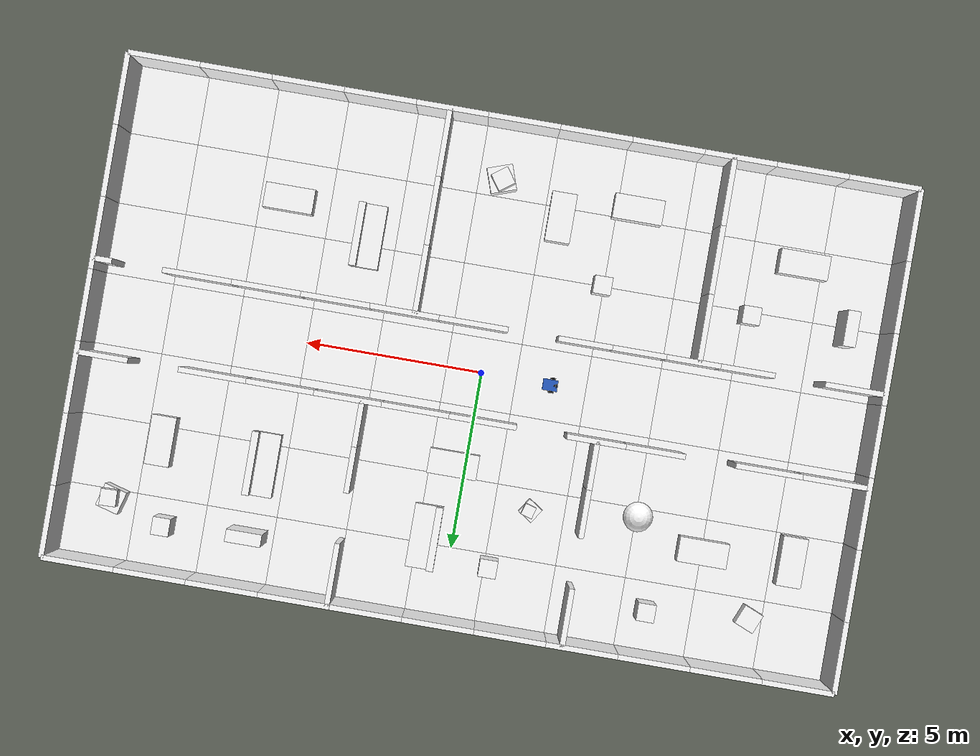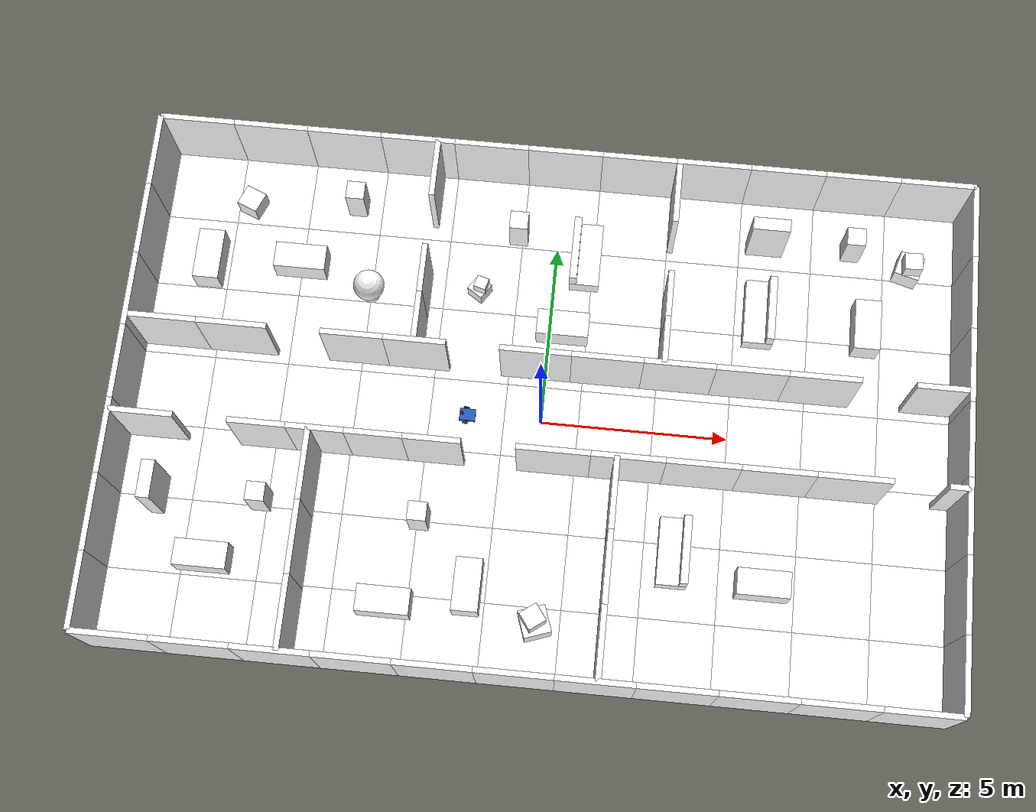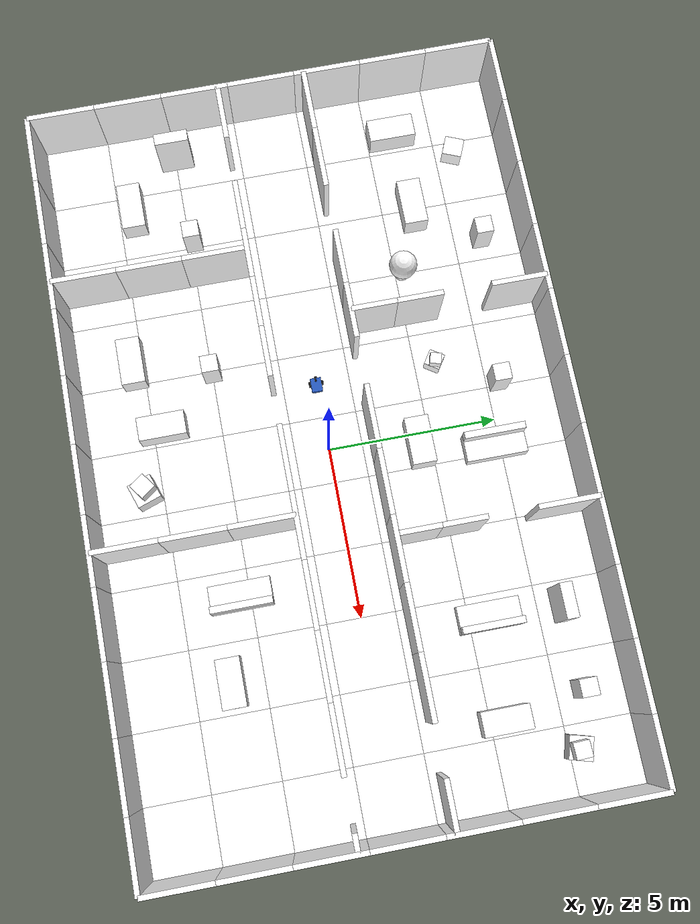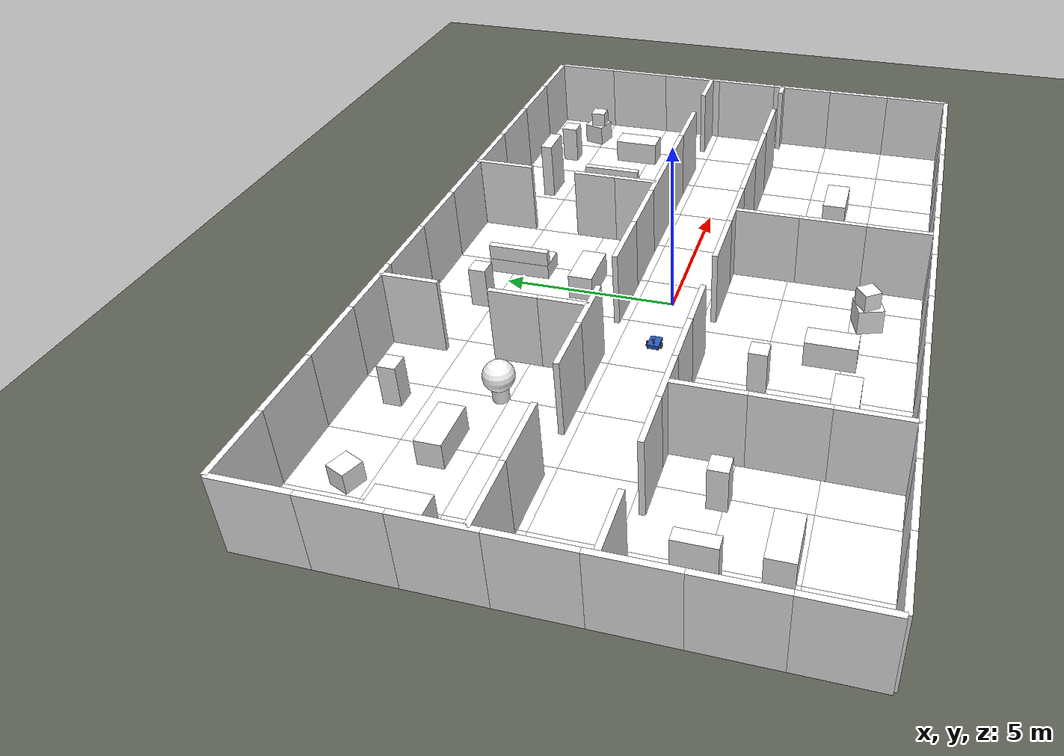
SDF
<?xml version="1.0" ?>
<!-- Generated by tools/generate_worlds.py (seeded procedural world). Do not edit by hand; re-generate instead. -->
<sdf version="1.9">
  <world name="office_0">
    <physics name="2ms" type="ignored">
      <max_step_size>0.002</max_step_size>
      <real_time_factor>1.0</real_time_factor>
    </physics>
    <plugin filename="gz-sim-physics-system" name="gz::sim::systems::Physics"/>
    <plugin filename="gz-sim-user-commands-system" name="gz::sim::systems::UserCommands"/>
    <plugin filename="gz-sim-scene-broadcaster-system" name="gz::sim::systems::SceneBroadcaster"/>
    <plugin filename="gz-sim-sensors-system" name="gz::sim::systems::Sensors">
      <render_engine>ogre2</render_engine>
    </plugin>

    <scene>
      <ambient>0.6 0.6 0.6 1</ambient>
      <background>0.70 0.80 0.95 1</background>
      <shadows>true</shadows>
      <grid>false</grid>
      <sky></sky>
    </scene>

    <light type="directional" name="sun">
      <cast_shadows>true</cast_shadows>
      <pose>0 0 20 0 0 0</pose>
      <diffuse>0.95 0.93 0.88 1</diffuse>
      <specular>0.3 0.3 0.3 1</specular>
      <direction>-0.4 0.25 -0.88</direction>
    </light>

    <model name="ground_plane">
      <static>true</static>
      <link name="link">
        <collision name="collision">
          <geometry><plane><normal>0 0 1</normal><size>300.000 300.000</size></plane></geometry>
          <surface><friction><ode><mu>1.0</mu><mu2>1.0</mu2></ode></friction></surface>
        </collision>
        <visual name="visual">
          <geometry><plane><normal>0 0 1</normal><size>300.000 300.000</size></plane></geometry>
          <material><ambient>0.350 0.370 0.330 1</ambient><diffuse>0.350 0.370 0.330 1</diffuse><specular>0.08 0.08 0.08 1</specular></material>
        </visual>
      </link>
    </model>

    <model name="floor_1">
      <static>true</static>
      <pose>0.000 0.000 0.000 0.0000 0.0000 0.0000</pose>
      <link name="link">
        <visual name="v0"><pose>-10.000 -6.000 0.005 0.0000 0.0000 0.0000</pose><geometry><plane><normal>0 0 1</normal><size>2.000 2.000</size></plane></geometry><material><ambient>1.000 1.000 1.000 1</ambient><diffuse>1.000 1.000 1.000 1</diffuse><specular>0.08 0.08 0.08 1</specular><pbr><metal><albedo_map>model://omnivla_textures/materials/textures/paving.png</albedo_map><roughness>0.95</roughness><metalness>0.0</metalness></metal></pbr></material></visual>
        <visual name="v1"><pose>-10.000 -4.000 0.005 0.0000 0.0000 0.0000</pose><geometry><plane><normal>0 0 1</normal><size>2.000 2.000</size></plane></geometry><material><ambient>1.000 1.000 1.000 1</ambient><diffuse>1.000 1.000 1.000 1</diffuse><specular>0.08 0.08 0.08 1</specular><pbr><metal><albedo_map>model://omnivla_textures/materials/textures/paving.png</albedo_map><roughness>0.95</roughness><metalness>0.0</metalness></metal></pbr></material></visual>
        <visual name="v2"><pose>-10.000 -2.000 0.005 0.0000 0.0000 0.0000</pose><geometry><plane><normal>0 0 1</normal><size>2.000 2.000</size></plane></geometry><material><ambient>1.000 1.000 1.000 1</ambient><diffuse>1.000 1.000 1.000 1</diffuse><specular>0.08 0.08 0.08 1</specular><pbr><metal><albedo_map>model://omnivla_textures/materials/textures/paving.png</albedo_map><roughness>0.95</roughness><metalness>0.0</metalness></metal></pbr></material></visual>
        <visual name="v3"><pose>-10.000 0.000 0.005 0.0000 0.0000 0.0000</pose><geometry><plane><normal>0 0 1</normal><size>2.000 2.000</size></plane></geometry><material><ambient>1.000 1.000 1.000 1</ambient><diffuse>1.000 1.000 1.000 1</diffuse><specular>0.08 0.08 0.08 1</specular><pbr><metal><albedo_map>model://omnivla_textures/materials/textures/tile_floor_dark.png</albedo_map><roughness>0.95</roughness><metalness>0.0</metalness></metal></pbr></material></visual>
        <visual name="v4"><pose>-10.000 2.000 0.005 0.0000 0.0000 0.0000</pose><geometry><plane><normal>0 0 1</normal><size>2.000 2.000</size></plane></geometry><material><ambient>1.000 1.000 1.000 1</ambient><diffuse>1.000 1.000 1.000 1</diffuse><specular>0.08 0.08 0.08 1</specular><pbr><metal><albedo_map>model://omnivla_textures/materials/textures/carpet_blue.png</albedo_map><roughness>0.95</roughness><metalness>0.0</metalness></metal></pbr></material></visual>
        <visual name="v5"><pose>-10.000 4.000 0.005 0.0000 0.0000 0.0000</pose><geometry><plane><normal>0 0 1</normal><size>2.000 2.000</size></plane></geometry><material><ambient>1.000 1.000 1.000 1</ambient><diffuse>1.000 1.000 1.000 1</diffuse><specular>0.08 0.08 0.08 1</specular><pbr><metal><albedo_map>model://omnivla_textures/materials/textures/carpet_blue.png</albedo_map><roughness>0.95</roughness><metalness>0.0</metalness></metal></pbr></material></visual>
        <visual name="v6"><pose>-10.000 6.000 0.005 0.0000 0.0000 0.0000</pose><geometry><plane><normal>0 0 1</normal><size>2.000 2.000</size></plane></geometry><material><ambient>1.000 1.000 1.000 1</ambient><diffuse>1.000 1.000 1.000 1</diffuse><specular>0.08 0.08 0.08 1</specular><pbr><metal><albedo_map>model://omnivla_textures/materials/textures/carpet_blue.png</albedo_map><roughness>0.95</roughness><metalness>0.0</metalness></metal></pbr></material></visual>
        <visual name="v7"><pose>-8.000 -6.000 0.005 0.0000 0.0000 0.0000</pose><geometry><plane><normal>0 0 1</normal><size>2.000 2.000</size></plane></geometry><material><ambient>1.000 1.000 1.000 1</ambient><diffuse>1.000 1.000 1.000 1</diffuse><specular>0.08 0.08 0.08 1</specular><pbr><metal><albedo_map>model://omnivla_textures/materials/textures/paving.png</albedo_map><roughness>0.95</roughness><metalness>0.0</metalness></metal></pbr></material></visual>
        <visual name="v8"><pose>-8.000 -4.000 0.005 0.0000 0.0000 0.0000</pose><geometry><plane><normal>0 0 1</normal><size>2.000 2.000</size></plane></geometry><material><ambient>1.000 1.000 1.000 1</ambient><diffuse>1.000 1.000 1.000 1</diffuse><specular>0.08 0.08 0.08 1</specular><pbr><metal><albedo_map>model://omnivla_textures/materials/textures/paving.png</albedo_map><roughness>0.95</roughness><metalness>0.0</metalness></metal></pbr></material></visual>
        <visual name="v9"><pose>-8.000 -2.000 0.005 0.0000 0.0000 0.0000</pose><geometry><plane><normal>0 0 1</normal><size>2.000 2.000</size></plane></geometry><material><ambient>1.000 1.000 1.000 1</ambient><diffuse>1.000 1.000 1.000 1</diffuse><specular>0.08 0.08 0.08 1</specular><pbr><metal><albedo_map>model://omnivla_textures/materials/textures/paving.png</albedo_map><roughness>0.95</roughness><metalness>0.0</metalness></metal></pbr></material></visual>
        <visual name="v10"><pose>-8.000 0.000 0.005 0.0000 0.0000 0.0000</pose><geometry><plane><normal>0 0 1</normal><size>2.000 2.000</size></plane></geometry><material><ambient>1.000 1.000 1.000 1</ambient><diffuse>1.000 1.000 1.000 1</diffuse><specular>0.08 0.08 0.08 1</specular><pbr><metal><albedo_map>model://omnivla_textures/materials/textures/tile_floor_dark.png</albedo_map><roughness>0.95</roughness><metalness>0.0</metalness></metal></pbr></material></visual>
        <visual name="v11"><pose>-8.000 2.000 0.005 0.0000 0.0000 0.0000</pose><geometry><plane><normal>0 0 1</normal><size>2.000 2.000</size></plane></geometry><material><ambient>1.000 1.000 1.000 1</ambient><diffuse>1.000 1.000 1.000 1</diffuse><specular>0.08 0.08 0.08 1</specular><pbr><metal><albedo_map>model://omnivla_textures/materials/textures/carpet_blue.png</albedo_map><roughness>0.95</roughness><metalness>0.0</metalness></metal></pbr></material></visual>
        <visual name="v12"><pose>-8.000 4.000 0.005 0.0000 0.0000 0.0000</pose><geometry><plane><normal>0 0 1</normal><size>2.000 2.000</size></plane></geometry><material><ambient>1.000 1.000 1.000 1</ambient><diffuse>1.000 1.000 1.000 1</diffuse><specular>0.08 0.08 0.08 1</specular><pbr><metal><albedo_map>model://omnivla_textures/materials/textures/carpet_blue.png</albedo_map><roughness>0.95</roughness><metalness>0.0</metalness></metal></pbr></material></visual>
        <visual name="v13"><pose>-8.000 6.000 0.005 0.0000 0.0000 0.0000</pose><geometry><plane><normal>0 0 1</normal><size>2.000 2.000</size></plane></geometry><material><ambient>1.000 1.000 1.000 1</ambient><diffuse>1.000 1.000 1.000 1</diffuse><specular>0.08 0.08 0.08 1</specular><pbr><metal><albedo_map>model://omnivla_textures/materials/textures/carpet_blue.png</albedo_map><roughness>0.95</roughness><metalness>0.0</metalness></metal></pbr></material></visual>
        <visual name="v14"><pose>-6.000 -6.000 0.005 0.0000 0.0000 0.0000</pose><geometry><plane><normal>0 0 1</normal><size>2.000 2.000</size></plane></geometry><material><ambient>1.000 1.000 1.000 1</ambient><diffuse>1.000 1.000 1.000 1</diffuse><specular>0.08 0.08 0.08 1</specular><pbr><metal><albedo_map>model://omnivla_textures/materials/textures/paving.png</albedo_map><roughness>0.95</roughness><metalness>0.0</metalness></metal></pbr></material></visual>
        <visual name="v15"><pose>-6.000 -4.000 0.005 0.0000 0.0000 0.0000</pose><geometry><plane><normal>0 0 1</normal><size>2.000 2.000</size></plane></geometry><material><ambient>1.000 1.000 1.000 1</ambient><diffuse>1.000 1.000 1.000 1</diffuse><specular>0.08 0.08 0.08 1</specular><pbr><metal><albedo_map>model://omnivla_textures/materials/textures/paving.png</albedo_map><roughness>0.95</roughness><metalness>0.0</metalness></metal></pbr></material></visual>
        <visual name="v16"><pose>-6.000 -2.000 0.005 0.0000 0.0000 0.0000</pose><geometry><plane><normal>0 0 1</normal><size>2.000 2.000</size></plane></geometry><material><ambient>1.000 1.000 1.000 1</ambient><diffuse>1.000 1.000 1.000 1</diffuse><specular>0.08 0.08 0.08 1</specular><pbr><metal><albedo_map>model://omnivla_textures/materials/textures/paving.png</albedo_map><roughness>0.95</roughness><metalness>0.0</metalness></metal></pbr></material></visual>
        <visual name="v17"><pose>-6.000 0.000 0.005 0.0000 0.0000 0.0000</pose><geometry><plane><normal>0 0 1</normal><size>2.000 2.000</size></plane></geometry><material><ambient>1.000 1.000 1.000 1</ambient><diffuse>1.000 1.000 1.000 1</diffuse><specular>0.08 0.08 0.08 1</specular><pbr><metal><albedo_map>model://omnivla_textures/materials/textures/tile_floor_dark.png</albedo_map><roughness>0.95</roughness><metalness>0.0</metalness></metal></pbr></material></visual>
        <visual name="v18"><pose>-6.000 2.000 0.005 0.0000 0.0000 0.0000</pose><geometry><plane><normal>0 0 1</normal><size>2.000 2.000</size></plane></geometry><material><ambient>1.000 1.000 1.000 1</ambient><diffuse>1.000 1.000 1.000 1</diffuse><specular>0.08 0.08 0.08 1</specular><pbr><metal><albedo_map>model://omnivla_textures/materials/textures/carpet_blue.png</albedo_map><roughness>0.95</roughness><metalness>0.0</metalness></metal></pbr></material></visual>
        <visual name="v19"><pose>-6.000 4.000 0.005 0.0000 0.0000 0.0000</pose><geometry><plane><normal>0 0 1</normal><size>2.000 2.000</size></plane></geometry><material><ambient>1.000 1.000 1.000 1</ambient><diffuse>1.000 1.000 1.000 1</diffuse><specular>0.08 0.08 0.08 1</specular><pbr><metal><albedo_map>model://omnivla_textures/materials/textures/carpet_blue.png</albedo_map><roughness>0.95</roughness><metalness>0.0</metalness></metal></pbr></material></visual>
        <visual name="v20"><pose>-6.000 6.000 0.005 0.0000 0.0000 0.0000</pose><geometry><plane><normal>0 0 1</normal><size>2.000 2.000</size></plane></geometry><material><ambient>1.000 1.000 1.000 1</ambient><diffuse>1.000 1.000 1.000 1</diffuse><specular>0.08 0.08 0.08 1</specular><pbr><metal><albedo_map>model://omnivla_textures/materials/textures/carpet_blue.png</albedo_map><roughness>0.95</roughness><metalness>0.0</metalness></metal></pbr></material></visual>
        <visual name="v21"><pose>-4.000 -6.000 0.005 0.0000 0.0000 0.0000</pose><geometry><plane><normal>0 0 1</normal><size>2.000 2.000</size></plane></geometry><material><ambient>1.000 1.000 1.000 1</ambient><diffuse>1.000 1.000 1.000 1</diffuse><specular>0.08 0.08 0.08 1</specular><pbr><metal><albedo_map>model://omnivla_textures/materials/textures/carpet_red.png</albedo_map><roughness>0.95</roughness><metalness>0.0</metalness></metal></pbr></material></visual>
        <visual name="v22"><pose>-4.000 -4.000 0.005 0.0000 0.0000 0.0000</pose><geometry><plane><normal>0 0 1</normal><size>2.000 2.000</size></plane></geometry><material><ambient>1.000 1.000 1.000 1</ambient><diffuse>1.000 1.000 1.000 1</diffuse><specular>0.08 0.08 0.08 1</specular><pbr><metal><albedo_map>model://omnivla_textures/materials/textures/carpet_red.png</albedo_map><roughness>0.95</roughness><metalness>0.0</metalness></metal></pbr></material></visual>
        <visual name="v23"><pose>-4.000 -2.000 0.005 0.0000 0.0000 0.0000</pose><geometry><plane><normal>0 0 1</normal><size>2.000 2.000</size></plane></geometry><material><ambient>1.000 1.000 1.000 1</ambient><diffuse>1.000 1.000 1.000 1</diffuse><specular>0.08 0.08 0.08 1</specular><pbr><metal><albedo_map>model://omnivla_textures/materials/textures/carpet_red.png</albedo_map><roughness>0.95</roughness><metalness>0.0</metalness></metal></pbr></material></visual>
        <visual name="v24"><pose>-4.000 0.000 0.005 0.0000 0.0000 0.0000</pose><geometry><plane><normal>0 0 1</normal><size>2.000 2.000</size></plane></geometry><material><ambient>1.000 1.000 1.000 1</ambient><diffuse>1.000 1.000 1.000 1</diffuse><specular>0.08 0.08 0.08 1</specular><pbr><metal><albedo_map>model://omnivla_textures/materials/textures/tile_floor_dark.png</albedo_map><roughness>0.95</roughness><metalness>0.0</metalness></metal></pbr></material></visual>
        <visual name="v25"><pose>-4.000 2.000 0.005 0.0000 0.0000 0.0000</pose><geometry><plane><normal>0 0 1</normal><size>2.000 2.000</size></plane></geometry><material><ambient>1.000 1.000 1.000 1</ambient><diffuse>1.000 1.000 1.000 1</diffuse><specular>0.08 0.08 0.08 1</specular><pbr><metal><albedo_map>model://omnivla_textures/materials/textures/carpet_blue.png</albedo_map><roughness>0.95</roughness><metalness>0.0</metalness></metal></pbr></material></visual>
        <visual name="v26"><pose>-4.000 4.000 0.005 0.0000 0.0000 0.0000</pose><geometry><plane><normal>0 0 1</normal><size>2.000 2.000</size></plane></geometry><material><ambient>1.000 1.000 1.000 1</ambient><diffuse>1.000 1.000 1.000 1</diffuse><specular>0.08 0.08 0.08 1</specular><pbr><metal><albedo_map>model://omnivla_textures/materials/textures/carpet_blue.png</albedo_map><roughness>0.95</roughness><metalness>0.0</metalness></metal></pbr></material></visual>
        <visual name="v27"><pose>-4.000 6.000 0.005 0.0000 0.0000 0.0000</pose><geometry><plane><normal>0 0 1</normal><size>2.000 2.000</size></plane></geometry><material><ambient>1.000 1.000 1.000 1</ambient><diffuse>1.000 1.000 1.000 1</diffuse><specular>0.08 0.08 0.08 1</specular><pbr><metal><albedo_map>model://omnivla_textures/materials/textures/carpet_blue.png</albedo_map><roughness>0.95</roughness><metalness>0.0</metalness></metal></pbr></material></visual>
        <visual name="v28"><pose>-2.000 -6.000 0.005 0.0000 0.0000 0.0000</pose><geometry><plane><normal>0 0 1</normal><size>2.000 2.000</size></plane></geometry><material><ambient>1.000 1.000 1.000 1</ambient><diffuse>1.000 1.000 1.000 1</diffuse><specular>0.08 0.08 0.08 1</specular><pbr><metal><albedo_map>model://omnivla_textures/materials/textures/carpet_red.png</albedo_map><roughness>0.95</roughness><metalness>0.0</metalness></metal></pbr></material></visual>
        <visual name="v29"><pose>-2.000 -4.000 0.005 0.0000 0.0000 0.0000</pose><geometry><plane><normal>0 0 1</normal><size>2.000 2.000</size></plane></geometry><material><ambient>1.000 1.000 1.000 1</ambient><diffuse>1.000 1.000 1.000 1</diffuse><specular>0.08 0.08 0.08 1</specular><pbr><metal><albedo_map>model://omnivla_textures/materials/textures/carpet_red.png</albedo_map><roughness>0.95</roughness><metalness>0.0</metalness></metal></pbr></material></visual>
        <visual name="v30"><pose>-2.000 -2.000 0.005 0.0000 0.0000 0.0000</pose><geometry><plane><normal>0 0 1</normal><size>2.000 2.000</size></plane></geometry><material><ambient>1.000 1.000 1.000 1</ambient><diffuse>1.000 1.000 1.000 1</diffuse><specular>0.08 0.08 0.08 1</specular><pbr><metal><albedo_map>model://omnivla_textures/materials/textures/carpet_red.png</albedo_map><roughness>0.95</roughness><metalness>0.0</metalness></metal></pbr></material></visual>
        <visual name="v31"><pose>-2.000 0.000 0.005 0.0000 0.0000 0.0000</pose><geometry><plane><normal>0 0 1</normal><size>2.000 2.000</size></plane></geometry><material><ambient>1.000 1.000 1.000 1</ambient><diffuse>1.000 1.000 1.000 1</diffuse><specular>0.08 0.08 0.08 1</specular><pbr><metal><albedo_map>model://omnivla_textures/materials/textures/tile_floor_dark.png</albedo_map><roughness>0.95</roughness><metalness>0.0</metalness></metal></pbr></material></visual>
        <visual name="v32"><pose>-2.000 2.000 0.005 0.0000 0.0000 0.0000</pose><geometry><plane><normal>0 0 1</normal><size>2.000 2.000</size></plane></geometry><material><ambient>1.000 1.000 1.000 1</ambient><diffuse>1.000 1.000 1.000 1</diffuse><specular>0.08 0.08 0.08 1</specular><pbr><metal><albedo_map>model://omnivla_textures/materials/textures/tile_floor.png</albedo_map><roughness>0.95</roughness><metalness>0.0</metalness></metal></pbr></material></visual>
        <visual name="v33"><pose>-2.000 4.000 0.005 0.0000 0.0000 0.0000</pose><geometry><plane><normal>0 0 1</normal><size>2.000 2.000</size></plane></geometry><material><ambient>1.000 1.000 1.000 1</ambient><diffuse>1.000 1.000 1.000 1</diffuse><specular>0.08 0.08 0.08 1</specular><pbr><metal><albedo_map>model://omnivla_textures/materials/textures/tile_floor.png</albedo_map><roughness>0.95</roughness><metalness>0.0</metalness></metal></pbr></material></visual>
        <visual name="v34"><pose>-2.000 6.000 0.005 0.0000 0.0000 0.0000</pose><geometry><plane><normal>0 0 1</normal><size>2.000 2.000</size></plane></geometry><material><ambient>1.000 1.000 1.000 1</ambient><diffuse>1.000 1.000 1.000 1</diffuse><specular>0.08 0.08 0.08 1</specular><pbr><metal><albedo_map>model://omnivla_textures/materials/textures/tile_floor.png</albedo_map><roughness>0.95</roughness><metalness>0.0</metalness></metal></pbr></material></visual>
        <visual name="v35"><pose>0.000 -6.000 0.005 0.0000 0.0000 0.0000</pose><geometry><plane><normal>0 0 1</normal><size>2.000 2.000</size></plane></geometry><material><ambient>1.000 1.000 1.000 1</ambient><diffuse>1.000 1.000 1.000 1</diffuse><specular>0.08 0.08 0.08 1</specular><pbr><metal><albedo_map>model://omnivla_textures/materials/textures/carpet_red.png</albedo_map><roughness>0.95</roughness><metalness>0.0</metalness></metal></pbr></material></visual>
        <visual name="v36"><pose>0.000 -4.000 0.005 0.0000 0.0000 0.0000</pose><geometry><plane><normal>0 0 1</normal><size>2.000 2.000</size></plane></geometry><material><ambient>1.000 1.000 1.000 1</ambient><diffuse>1.000 1.000 1.000 1</diffuse><specular>0.08 0.08 0.08 1</specular><pbr><metal><albedo_map>model://omnivla_textures/materials/textures/carpet_red.png</albedo_map><roughness>0.95</roughness><metalness>0.0</metalness></metal></pbr></material></visual>
        <visual name="v37"><pose>0.000 -2.000 0.005 0.0000 0.0000 0.0000</pose><geometry><plane><normal>0 0 1</normal><size>2.000 2.000</size></plane></geometry><material><ambient>1.000 1.000 1.000 1</ambient><diffuse>1.000 1.000 1.000 1</diffuse><specular>0.08 0.08 0.08 1</specular><pbr><metal><albedo_map>model://omnivla_textures/materials/textures/carpet_red.png</albedo_map><roughness>0.95</roughness><metalness>0.0</metalness></metal></pbr></material></visual>
        <visual name="v38"><pose>0.000 0.000 0.005 0.0000 0.0000 0.0000</pose><geometry><plane><normal>0 0 1</normal><size>2.000 2.000</size></plane></geometry><material><ambient>1.000 1.000 1.000 1</ambient><diffuse>1.000 1.000 1.000 1</diffuse><specular>0.08 0.08 0.08 1</specular><pbr><metal><albedo_map>model://omnivla_textures/materials/textures/tile_floor_dark.png</albedo_map><roughness>0.95</roughness><metalness>0.0</metalness></metal></pbr></material></visual>
        <visual name="v39"><pose>0.000 2.000 0.005 0.0000 0.0000 0.0000</pose><geometry><plane><normal>0 0 1</normal><size>2.000 2.000</size></plane></geometry><material><ambient>1.000 1.000 1.000 1</ambient><diffuse>1.000 1.000 1.000 1</diffuse><specular>0.08 0.08 0.08 1</specular><pbr><metal><albedo_map>model://omnivla_textures/materials/textures/tile_floor.png</albedo_map><roughness>0.95</roughness><metalness>0.0</metalness></metal></pbr></material></visual>
        <visual name="v40"><pose>0.000 4.000 0.005 0.0000 0.0000 0.0000</pose><geometry><plane><normal>0 0 1</normal><size>2.000 2.000</size></plane></geometry><material><ambient>1.000 1.000 1.000 1</ambient><diffuse>1.000 1.000 1.000 1</diffuse><specular>0.08 0.08 0.08 1</specular><pbr><metal><albedo_map>model://omnivla_textures/materials/textures/tile_floor.png</albedo_map><roughness>0.95</roughness><metalness>0.0</metalness></metal></pbr></material></visual>
        <visual name="v41"><pose>0.000 6.000 0.005 0.0000 0.0000 0.0000</pose><geometry><plane><normal>0 0 1</normal><size>2.000 2.000</size></plane></geometry><material><ambient>1.000 1.000 1.000 1</ambient><diffuse>1.000 1.000 1.000 1</diffuse><specular>0.08 0.08 0.08 1</specular><pbr><metal><albedo_map>model://omnivla_textures/materials/textures/tile_floor.png</albedo_map><roughness>0.95</roughness><metalness>0.0</metalness></metal></pbr></material></visual>
        <visual name="v42"><pose>2.000 -6.000 0.005 0.0000 0.0000 0.0000</pose><geometry><plane><normal>0 0 1</normal><size>2.000 2.000</size></plane></geometry><material><ambient>1.000 1.000 1.000 1</ambient><diffuse>1.000 1.000 1.000 1</diffuse><specular>0.08 0.08 0.08 1</specular><pbr><metal><albedo_map>model://omnivla_textures/materials/textures/carpet_red.png</albedo_map><roughness>0.95</roughness><metalness>0.0</metalness></metal></pbr></material></visual>
        <visual name="v43"><pose>2.000 -4.000 0.005 0.0000 0.0000 0.0000</pose><geometry><plane><normal>0 0 1</normal><size>2.000 2.000</size></plane></geometry><material><ambient>1.000 1.000 1.000 1</ambient><diffuse>1.000 1.000 1.000 1</diffuse><specular>0.08 0.08 0.08 1</specular><pbr><metal><albedo_map>model://omnivla_textures/materials/textures/carpet_red.png</albedo_map><roughness>0.95</roughness><metalness>0.0</metalness></metal></pbr></material></visual>
        <visual name="v44"><pose>2.000 -2.000 0.005 0.0000 0.0000 0.0000</pose><geometry><plane><normal>0 0 1</normal><size>2.000 2.000</size></plane></geometry><material><ambient>1.000 1.000 1.000 1</ambient><diffuse>1.000 1.000 1.000 1</diffuse><specular>0.08 0.08 0.08 1</specular><pbr><metal><albedo_map>model://omnivla_textures/materials/textures/carpet_red.png</albedo_map><roughness>0.95</roughness><metalness>0.0</metalness></metal></pbr></material></visual>
        <visual name="v45"><pose>2.000 0.000 0.005 0.0000 0.0000 0.0000</pose><geometry><plane><normal>0 0 1</normal><size>2.000 2.000</size></plane></geometry><material><ambient>1.000 1.000 1.000 1</ambient><diffuse>1.000 1.000 1.000 1</diffuse><specular>0.08 0.08 0.08 1</specular><pbr><metal><albedo_map>model://omnivla_textures/materials/textures/tile_floor_dark.png</albedo_map><roughness>0.95</roughness><metalness>0.0</metalness></metal></pbr></material></visual>
        <visual name="v46"><pose>2.000 2.000 0.005 0.0000 0.0000 0.0000</pose><geometry><plane><normal>0 0 1</normal><size>2.000 2.000</size></plane></geometry><material><ambient>1.000 1.000 1.000 1</ambient><diffuse>1.000 1.000 1.000 1</diffuse><specular>0.08 0.08 0.08 1</specular><pbr><metal><albedo_map>model://omnivla_textures/materials/textures/tile_floor.png</albedo_map><roughness>0.95</roughness><metalness>0.0</metalness></metal></pbr></material></visual>
        <visual name="v47"><pose>2.000 4.000 0.005 0.0000 0.0000 0.0000</pose><geometry><plane><normal>0 0 1</normal><size>2.000 2.000</size></plane></geometry><material><ambient>1.000 1.000 1.000 1</ambient><diffuse>1.000 1.000 1.000 1</diffuse><specular>0.08 0.08 0.08 1</specular><pbr><metal><albedo_map>model://omnivla_textures/materials/textures/tile_floor.png</albedo_map><roughness>0.95</roughness><metalness>0.0</metalness></metal></pbr></material></visual>
        <visual name="v48"><pose>2.000 6.000 0.005 0.0000 0.0000 0.0000</pose><geometry><plane><normal>0 0 1</normal><size>2.000 2.000</size></plane></geometry><material><ambient>1.000 1.000 1.000 1</ambient><diffuse>1.000 1.000 1.000 1</diffuse><specular>0.08 0.08 0.08 1</specular><pbr><metal><albedo_map>model://omnivla_textures/materials/textures/tile_floor.png</albedo_map><roughness>0.95</roughness><metalness>0.0</metalness></metal></pbr></material></visual>
        <visual name="v49"><pose>4.000 -6.000 0.005 0.0000 0.0000 0.0000</pose><geometry><plane><normal>0 0 1</normal><size>2.000 2.000</size></plane></geometry><material><ambient>1.000 1.000 1.000 1</ambient><diffuse>1.000 1.000 1.000 1</diffuse><specular>0.08 0.08 0.08 1</specular><pbr><metal><albedo_map>model://omnivla_textures/materials/textures/carpet_red.png</albedo_map><roughness>0.95</roughness><metalness>0.0</metalness></metal></pbr></material></visual>
        <visual name="v50"><pose>4.000 -4.000 0.005 0.0000 0.0000 0.0000</pose><geometry><plane><normal>0 0 1</normal><size>2.000 2.000</size></plane></geometry><material><ambient>1.000 1.000 1.000 1</ambient><diffuse>1.000 1.000 1.000 1</diffuse><specular>0.08 0.08 0.08 1</specular><pbr><metal><albedo_map>model://omnivla_textures/materials/textures/carpet_red.png</albedo_map><roughness>0.95</roughness><metalness>0.0</metalness></metal></pbr></material></visual>
        <visual name="v51"><pose>4.000 -2.000 0.005 0.0000 0.0000 0.0000</pose><geometry><plane><normal>0 0 1</normal><size>2.000 2.000</size></plane></geometry><material><ambient>1.000 1.000 1.000 1</ambient><diffuse>1.000 1.000 1.000 1</diffuse><specular>0.08 0.08 0.08 1</specular><pbr><metal><albedo_map>model://omnivla_textures/materials/textures/carpet_red.png</albedo_map><roughness>0.95</roughness><metalness>0.0</metalness></metal></pbr></material></visual>
        <visual name="v52"><pose>4.000 0.000 0.005 0.0000 0.0000 0.0000</pose><geometry><plane><normal>0 0 1</normal><size>2.000 2.000</size></plane></geometry><material><ambient>1.000 1.000 1.000 1</ambient><diffuse>1.000 1.000 1.000 1</diffuse><specular>0.08 0.08 0.08 1</specular><pbr><metal><albedo_map>model://omnivla_textures/materials/textures/tile_floor_dark.png</albedo_map><roughness>0.95</roughness><metalness>0.0</metalness></metal></pbr></material></visual>
        <visual name="v53"><pose>4.000 2.000 0.005 0.0000 0.0000 0.0000</pose><geometry><plane><normal>0 0 1</normal><size>2.000 2.000</size></plane></geometry><material><ambient>1.000 1.000 1.000 1</ambient><diffuse>1.000 1.000 1.000 1</diffuse><specular>0.08 0.08 0.08 1</specular><pbr><metal><albedo_map>model://omnivla_textures/materials/textures/carpet_red.png</albedo_map><roughness>0.95</roughness><metalness>0.0</metalness></metal></pbr></material></visual>
        <visual name="v54"><pose>4.000 4.000 0.005 0.0000 0.0000 0.0000</pose><geometry><plane><normal>0 0 1</normal><size>2.000 2.000</size></plane></geometry><material><ambient>1.000 1.000 1.000 1</ambient><diffuse>1.000 1.000 1.000 1</diffuse><specular>0.08 0.08 0.08 1</specular><pbr><metal><albedo_map>model://omnivla_textures/materials/textures/carpet_red.png</albedo_map><roughness>0.95</roughness><metalness>0.0</metalness></metal></pbr></material></visual>
        <visual name="v55"><pose>4.000 6.000 0.005 0.0000 0.0000 0.0000</pose><geometry><plane><normal>0 0 1</normal><size>2.000 2.000</size></plane></geometry><material><ambient>1.000 1.000 1.000 1</ambient><diffuse>1.000 1.000 1.000 1</diffuse><specular>0.08 0.08 0.08 1</specular><pbr><metal><albedo_map>model://omnivla_textures/materials/textures/carpet_red.png</albedo_map><roughness>0.95</roughness><metalness>0.0</metalness></metal></pbr></material></visual>
        <visual name="v56"><pose>6.000 -6.000 0.005 0.0000 0.0000 0.0000</pose><geometry><plane><normal>0 0 1</normal><size>2.000 2.000</size></plane></geometry><material><ambient>1.000 1.000 1.000 1</ambient><diffuse>1.000 1.000 1.000 1</diffuse><specular>0.08 0.08 0.08 1</specular><pbr><metal><albedo_map>model://omnivla_textures/materials/textures/carpet_red.png</albedo_map><roughness>0.95</roughness><metalness>0.0</metalness></metal></pbr></material></visual>
        <visual name="v57"><pose>6.000 -4.000 0.005 0.0000 0.0000 0.0000</pose><geometry><plane><normal>0 0 1</normal><size>2.000 2.000</size></plane></geometry><material><ambient>1.000 1.000 1.000 1</ambient><diffuse>1.000 1.000 1.000 1</diffuse><specular>0.08 0.08 0.08 1</specular><pbr><metal><albedo_map>model://omnivla_textures/materials/textures/carpet_red.png</albedo_map><roughness>0.95</roughness><metalness>0.0</metalness></metal></pbr></material></visual>
        <visual name="v58"><pose>6.000 -2.000 0.005 0.0000 0.0000 0.0000</pose><geometry><plane><normal>0 0 1</normal><size>2.000 2.000</size></plane></geometry><material><ambient>1.000 1.000 1.000 1</ambient><diffuse>1.000 1.000 1.000 1</diffuse><specular>0.08 0.08 0.08 1</specular><pbr><metal><albedo_map>model://omnivla_textures/materials/textures/carpet_red.png</albedo_map><roughness>0.95</roughness><metalness>0.0</metalness></metal></pbr></material></visual>
        <visual name="v59"><pose>6.000 0.000 0.005 0.0000 0.0000 0.0000</pose><geometry><plane><normal>0 0 1</normal><size>2.000 2.000</size></plane></geometry><material><ambient>1.000 1.000 1.000 1</ambient><diffuse>1.000 1.000 1.000 1</diffuse><specular>0.08 0.08 0.08 1</specular><pbr><metal><albedo_map>model://omnivla_textures/materials/textures/tile_floor_dark.png</albedo_map><roughness>0.95</roughness><metalness>0.0</metalness></metal></pbr></material></visual>
        <visual name="v60"><pose>6.000 2.000 0.005 0.0000 0.0000 0.0000</pose><geometry><plane><normal>0 0 1</normal><size>2.000 2.000</size></plane></geometry><material><ambient>1.000 1.000 1.000 1</ambient><diffuse>1.000 1.000 1.000 1</diffuse><specular>0.08 0.08 0.08 1</specular><pbr><metal><albedo_map>model://omnivla_textures/materials/textures/carpet_red.png</albedo_map><roughness>0.95</roughness><metalness>0.0</metalness></metal></pbr></material></visual>
        <visual name="v61"><pose>6.000 4.000 0.005 0.0000 0.0000 0.0000</pose><geometry><plane><normal>0 0 1</normal><size>2.000 2.000</size></plane></geometry><material><ambient>1.000 1.000 1.000 1</ambient><diffuse>1.000 1.000 1.000 1</diffuse><specular>0.08 0.08 0.08 1</specular><pbr><metal><albedo_map>model://omnivla_textures/materials/textures/carpet_red.png</albedo_map><roughness>0.95</roughness><metalness>0.0</metalness></metal></pbr></material></visual>
        <visual name="v62"><pose>6.000 6.000 0.005 0.0000 0.0000 0.0000</pose><geometry><plane><normal>0 0 1</normal><size>2.000 2.000</size></plane></geometry><material><ambient>1.000 1.000 1.000 1</ambient><diffuse>1.000 1.000 1.000 1</diffuse><specular>0.08 0.08 0.08 1</specular><pbr><metal><albedo_map>model://omnivla_textures/materials/textures/carpet_red.png</albedo_map><roughness>0.95</roughness><metalness>0.0</metalness></metal></pbr></material></visual>
        <visual name="v63"><pose>8.000 -6.000 0.005 0.0000 0.0000 0.0000</pose><geometry><plane><normal>0 0 1</normal><size>2.000 2.000</size></plane></geometry><material><ambient>1.000 1.000 1.000 1</ambient><diffuse>1.000 1.000 1.000 1</diffuse><specular>0.08 0.08 0.08 1</specular><pbr><metal><albedo_map>model://omnivla_textures/materials/textures/carpet_red.png</albedo_map><roughness>0.95</roughness><metalness>0.0</metalness></metal></pbr></material></visual>
        <visual name="v64"><pose>8.000 -4.000 0.005 0.0000 0.0000 0.0000</pose><geometry><plane><normal>0 0 1</normal><size>2.000 2.000</size></plane></geometry><material><ambient>1.000 1.000 1.000 1</ambient><diffuse>1.000 1.000 1.000 1</diffuse><specular>0.08 0.08 0.08 1</specular><pbr><metal><albedo_map>model://omnivla_textures/materials/textures/carpet_red.png</albedo_map><roughness>0.95</roughness><metalness>0.0</metalness></metal></pbr></material></visual>
        <visual name="v65"><pose>8.000 -2.000 0.005 0.0000 0.0000 0.0000</pose><geometry><plane><normal>0 0 1</normal><size>2.000 2.000</size></plane></geometry><material><ambient>1.000 1.000 1.000 1</ambient><diffuse>1.000 1.000 1.000 1</diffuse><specular>0.08 0.08 0.08 1</specular><pbr><metal><albedo_map>model://omnivla_textures/materials/textures/carpet_red.png</albedo_map><roughness>0.95</roughness><metalness>0.0</metalness></metal></pbr></material></visual>
        <visual name="v66"><pose>8.000 0.000 0.005 0.0000 0.0000 0.0000</pose><geometry><plane><normal>0 0 1</normal><size>2.000 2.000</size></plane></geometry><material><ambient>1.000 1.000 1.000 1</ambient><diffuse>1.000 1.000 1.000 1</diffuse><specular>0.08 0.08 0.08 1</specular><pbr><metal><albedo_map>model://omnivla_textures/materials/textures/tile_floor_dark.png</albedo_map><roughness>0.95</roughness><metalness>0.0</metalness></metal></pbr></material></visual>
        <visual name="v67"><pose>8.000 2.000 0.005 0.0000 0.0000 0.0000</pose><geometry><plane><normal>0 0 1</normal><size>2.000 2.000</size></plane></geometry><material><ambient>1.000 1.000 1.000 1</ambient><diffuse>1.000 1.000 1.000 1</diffuse><specular>0.08 0.08 0.08 1</specular><pbr><metal><albedo_map>model://omnivla_textures/materials/textures/carpet_red.png</albedo_map><roughness>0.95</roughness><metalness>0.0</metalness></metal></pbr></material></visual>
        <visual name="v68"><pose>8.000 4.000 0.005 0.0000 0.0000 0.0000</pose><geometry><plane><normal>0 0 1</normal><size>2.000 2.000</size></plane></geometry><material><ambient>1.000 1.000 1.000 1</ambient><diffuse>1.000 1.000 1.000 1</diffuse><specular>0.08 0.08 0.08 1</specular><pbr><metal><albedo_map>model://omnivla_textures/materials/textures/carpet_red.png</albedo_map><roughness>0.95</roughness><metalness>0.0</metalness></metal></pbr></material></visual>
        <visual name="v69"><pose>8.000 6.000 0.005 0.0000 0.0000 0.0000</pose><geometry><plane><normal>0 0 1</normal><size>2.000 2.000</size></plane></geometry><material><ambient>1.000 1.000 1.000 1</ambient><diffuse>1.000 1.000 1.000 1</diffuse><specular>0.08 0.08 0.08 1</specular><pbr><metal><albedo_map>model://omnivla_textures/materials/textures/carpet_red.png</albedo_map><roughness>0.95</roughness><metalness>0.0</metalness></metal></pbr></material></visual>
        <visual name="v70"><pose>10.000 -6.000 0.005 0.0000 0.0000 0.0000</pose><geometry><plane><normal>0 0 1</normal><size>2.000 2.000</size></plane></geometry><material><ambient>1.000 1.000 1.000 1</ambient><diffuse>1.000 1.000 1.000 1</diffuse><specular>0.08 0.08 0.08 1</specular><pbr><metal><albedo_map>model://omnivla_textures/materials/textures/carpet_red.png</albedo_map><roughness>0.95</roughness><metalness>0.0</metalness></metal></pbr></material></visual>
        <visual name="v71"><pose>10.000 -4.000 0.005 0.0000 0.0000 0.0000</pose><geometry><plane><normal>0 0 1</normal><size>2.000 2.000</size></plane></geometry><material><ambient>1.000 1.000 1.000 1</ambient><diffuse>1.000 1.000 1.000 1</diffuse><specular>0.08 0.08 0.08 1</specular><pbr><metal><albedo_map>model://omnivla_textures/materials/textures/carpet_red.png</albedo_map><roughness>0.95</roughness><metalness>0.0</metalness></metal></pbr></material></visual>
        <visual name="v72"><pose>10.000 -2.000 0.005 0.0000 0.0000 0.0000</pose><geometry><plane><normal>0 0 1</normal><size>2.000 2.000</size></plane></geometry><material><ambient>1.000 1.000 1.000 1</ambient><diffuse>1.000 1.000 1.000 1</diffuse><specular>0.08 0.08 0.08 1</specular><pbr><metal><albedo_map>model://omnivla_textures/materials/textures/carpet_red.png</albedo_map><roughness>0.95</roughness><metalness>0.0</metalness></metal></pbr></material></visual>
        <visual name="v73"><pose>10.000 0.000 0.005 0.0000 0.0000 0.0000</pose><geometry><plane><normal>0 0 1</normal><size>2.000 2.000</size></plane></geometry><material><ambient>1.000 1.000 1.000 1</ambient><diffuse>1.000 1.000 1.000 1</diffuse><specular>0.08 0.08 0.08 1</specular><pbr><metal><albedo_map>model://omnivla_textures/materials/textures/tile_floor_dark.png</albedo_map><roughness>0.95</roughness><metalness>0.0</metalness></metal></pbr></material></visual>
        <visual name="v74"><pose>10.000 2.000 0.005 0.0000 0.0000 0.0000</pose><geometry><plane><normal>0 0 1</normal><size>2.000 2.000</size></plane></geometry><material><ambient>1.000 1.000 1.000 1</ambient><diffuse>1.000 1.000 1.000 1</diffuse><specular>0.08 0.08 0.08 1</specular><pbr><metal><albedo_map>model://omnivla_textures/materials/textures/carpet_red.png</albedo_map><roughness>0.95</roughness><metalness>0.0</metalness></metal></pbr></material></visual>
        <visual name="v75"><pose>10.000 4.000 0.005 0.0000 0.0000 0.0000</pose><geometry><plane><normal>0 0 1</normal><size>2.000 2.000</size></plane></geometry><material><ambient>1.000 1.000 1.000 1</ambient><diffuse>1.000 1.000 1.000 1</diffuse><specular>0.08 0.08 0.08 1</specular><pbr><metal><albedo_map>model://omnivla_textures/materials/textures/carpet_red.png</albedo_map><roughness>0.95</roughness><metalness>0.0</metalness></metal></pbr></material></visual>
        <visual name="v76"><pose>10.000 6.000 0.005 0.0000 0.0000 0.0000</pose><geometry><plane><normal>0 0 1</normal><size>2.000 2.000</size></plane></geometry><material><ambient>1.000 1.000 1.000 1</ambient><diffuse>1.000 1.000 1.000 1</diffuse><specular>0.08 0.08 0.08 1</specular><pbr><metal><albedo_map>model://omnivla_textures/materials/textures/carpet_red.png</albedo_map><roughness>0.95</roughness><metalness>0.0</metalness></metal></pbr></material></visual>
      </link>
    </model>
    <model name="wall_2">
      <static>true</static>
      <pose>0.000 0.000 0.000 0.0000 0.0000 0.0000</pose>
      <link name="link">
        <collision name="c0"><pose>-10.000 -7.000 1.100 0.0000 0.0000 0.0000</pose><geometry><box><size>2.002 0.150 2.200</size></box></geometry></collision>
        <visual name="v0"><pose>-10.000 -7.000 1.100 0.0000 0.0000 0.0000</pose><geometry><box><size>2.002 0.150 2.200</size></box></geometry><material><ambient>1.000 1.000 1.000 1</ambient><diffuse>1.000 1.000 1.000 1</diffuse><specular>0.08 0.08 0.08 1</specular><pbr><metal><albedo_map>model://omnivla_textures/materials/textures/brick_red.png</albedo_map><roughness>0.85</roughness><metalness>0.0</metalness></metal></pbr></material></visual>
        <collision name="c1"><pose>-8.000 -7.000 1.100 0.0000 0.0000 0.0000</pose><geometry><box><size>2.002 0.150 2.200</size></box></geometry></collision>
        <visual name="v1"><pose>-8.000 -7.000 1.100 0.0000 0.0000 0.0000</pose><geometry><box><size>2.002 0.150 2.200</size></box></geometry><material><ambient>1.000 1.000 1.000 1</ambient><diffuse>1.000 1.000 1.000 1</diffuse><specular>0.08 0.08 0.08 1</specular><pbr><metal><albedo_map>model://omnivla_textures/materials/textures/brick_red.png</albedo_map><roughness>0.85</roughness><metalness>0.0</metalness></metal></pbr></material></visual>
        <collision name="c2"><pose>-6.000 -7.000 1.100 0.0000 0.0000 0.0000</pose><geometry><box><size>2.002 0.150 2.200</size></box></geometry></collision>
        <visual name="v2"><pose>-6.000 -7.000 1.100 0.0000 0.0000 0.0000</pose><geometry><box><size>2.002 0.150 2.200</size></box></geometry><material><ambient>1.000 1.000 1.000 1</ambient><diffuse>1.000 1.000 1.000 1</diffuse><specular>0.08 0.08 0.08 1</specular><pbr><metal><albedo_map>model://omnivla_textures/materials/textures/brick_red.png</albedo_map><roughness>0.85</roughness><metalness>0.0</metalness></metal></pbr></material></visual>
        <collision name="c3"><pose>-4.000 -7.000 1.100 0.0000 0.0000 0.0000</pose><geometry><box><size>2.002 0.150 2.200</size></box></geometry></collision>
        <visual name="v3"><pose>-4.000 -7.000 1.100 0.0000 0.0000 0.0000</pose><geometry><box><size>2.002 0.150 2.200</size></box></geometry><material><ambient>1.000 1.000 1.000 1</ambient><diffuse>1.000 1.000 1.000 1</diffuse><specular>0.08 0.08 0.08 1</specular><pbr><metal><albedo_map>model://omnivla_textures/materials/textures/poster_6.png</albedo_map><roughness>0.85</roughness><metalness>0.0</metalness></metal></pbr></material></visual>
        <collision name="c4"><pose>-2.000 -7.000 1.100 0.0000 0.0000 0.0000</pose><geometry><box><size>2.002 0.150 2.200</size></box></geometry></collision>
        <visual name="v4"><pose>-2.000 -7.000 1.100 0.0000 0.0000 0.0000</pose><geometry><box><size>2.002 0.150 2.200</size></box></geometry><material><ambient>1.000 1.000 1.000 1</ambient><diffuse>1.000 1.000 1.000 1</diffuse><specular>0.08 0.08 0.08 1</specular><pbr><metal><albedo_map>model://omnivla_textures/materials/textures/brick_red.png</albedo_map><roughness>0.85</roughness><metalness>0.0</metalness></metal></pbr></material></visual>
        <collision name="c5"><pose>0.000 -7.000 1.100 0.0000 0.0000 0.0000</pose><geometry><box><size>2.002 0.150 2.200</size></box></geometry></collision>
        <visual name="v5"><pose>0.000 -7.000 1.100 0.0000 0.0000 0.0000</pose><geometry><box><size>2.002 0.150 2.200</size></box></geometry><material><ambient>1.000 1.000 1.000 1</ambient><diffuse>1.000 1.000 1.000 1</diffuse><specular>0.08 0.08 0.08 1</specular><pbr><metal><albedo_map>model://omnivla_textures/materials/textures/poster_6.png</albedo_map><roughness>0.85</roughness><metalness>0.0</metalness></metal></pbr></material></visual>
        <collision name="c6"><pose>2.000 -7.000 1.100 0.0000 0.0000 0.0000</pose><geometry><box><size>2.002 0.150 2.200</size></box></geometry></collision>
        <visual name="v6"><pose>2.000 -7.000 1.100 0.0000 0.0000 0.0000</pose><geometry><box><size>2.002 0.150 2.200</size></box></geometry><material><ambient>1.000 1.000 1.000 1</ambient><diffuse>1.000 1.000 1.000 1</diffuse><specular>0.08 0.08 0.08 1</specular><pbr><metal><albedo_map>model://omnivla_textures/materials/textures/brick_red.png</albedo_map><roughness>0.85</roughness><metalness>0.0</metalness></metal></pbr></material></visual>
        <collision name="c7"><pose>4.000 -7.000 1.100 0.0000 0.0000 0.0000</pose><geometry><box><size>2.002 0.150 2.200</size></box></geometry></collision>
        <visual name="v7"><pose>4.000 -7.000 1.100 0.0000 0.0000 0.0000</pose><geometry><box><size>2.002 0.150 2.200</size></box></geometry><material><ambient>1.000 1.000 1.000 1</ambient><diffuse>1.000 1.000 1.000 1</diffuse><specular>0.08 0.08 0.08 1</specular><pbr><metal><albedo_map>model://omnivla_textures/materials/textures/brick_red.png</albedo_map><roughness>0.85</roughness><metalness>0.0</metalness></metal></pbr></material></visual>
        <collision name="c8"><pose>6.000 -7.000 1.100 0.0000 0.0000 0.0000</pose><geometry><box><size>2.002 0.150 2.200</size></box></geometry></collision>
        <visual name="v8"><pose>6.000 -7.000 1.100 0.0000 0.0000 0.0000</pose><geometry><box><size>2.002 0.150 2.200</size></box></geometry><material><ambient>1.000 1.000 1.000 1</ambient><diffuse>1.000 1.000 1.000 1</diffuse><specular>0.08 0.08 0.08 1</specular><pbr><metal><albedo_map>model://omnivla_textures/materials/textures/brick_red.png</albedo_map><roughness>0.85</roughness><metalness>0.0</metalness></metal></pbr></material></visual>
        <collision name="c9"><pose>8.000 -7.000 1.100 0.0000 0.0000 0.0000</pose><geometry><box><size>2.002 0.150 2.200</size></box></geometry></collision>
        <visual name="v9"><pose>8.000 -7.000 1.100 0.0000 0.0000 0.0000</pose><geometry><box><size>2.002 0.150 2.200</size></box></geometry><material><ambient>1.000 1.000 1.000 1</ambient><diffuse>1.000 1.000 1.000 1</diffuse><specular>0.08 0.08 0.08 1</specular><pbr><metal><albedo_map>model://omnivla_textures/materials/textures/brick_red.png</albedo_map><roughness>0.85</roughness><metalness>0.0</metalness></metal></pbr></material></visual>
        <collision name="c10"><pose>10.000 -7.000 1.100 0.0000 0.0000 0.0000</pose><geometry><box><size>2.002 0.150 2.200</size></box></geometry></collision>
        <visual name="v10"><pose>10.000 -7.000 1.100 0.0000 0.0000 0.0000</pose><geometry><box><size>2.002 0.150 2.200</size></box></geometry><material><ambient>1.000 1.000 1.000 1</ambient><diffuse>1.000 1.000 1.000 1</diffuse><specular>0.08 0.08 0.08 1</specular><pbr><metal><albedo_map>model://omnivla_textures/materials/textures/brick_red.png</albedo_map><roughness>0.85</roughness><metalness>0.0</metalness></metal></pbr></material></visual>
      </link>
    </model>
    <model name="wall_3">
      <static>true</static>
      <pose>0.000 0.000 0.000 0.0000 0.0000 0.0000</pose>
      <link name="link">
        <collision name="c0"><pose>-10.000 7.000 1.100 0.0000 0.0000 0.0000</pose><geometry><box><size>2.002 0.150 2.200</size></box></geometry></collision>
        <visual name="v0"><pose>-10.000 7.000 1.100 0.0000 0.0000 0.0000</pose><geometry><box><size>2.002 0.150 2.200</size></box></geometry><material><ambient>1.000 1.000 1.000 1</ambient><diffuse>1.000 1.000 1.000 1</diffuse><specular>0.08 0.08 0.08 1</specular><pbr><metal><albedo_map>model://omnivla_textures/materials/textures/poster_0.png</albedo_map><roughness>0.85</roughness><metalness>0.0</metalness></metal></pbr></material></visual>
        <collision name="c1"><pose>-8.000 7.000 1.100 0.0000 0.0000 0.0000</pose><geometry><box><size>2.002 0.150 2.200</size></box></geometry></collision>
        <visual name="v1"><pose>-8.000 7.000 1.100 0.0000 0.0000 0.0000</pose><geometry><box><size>2.002 0.150 2.200</size></box></geometry><material><ambient>1.000 1.000 1.000 1</ambient><diffuse>1.000 1.000 1.000 1</diffuse><specular>0.08 0.08 0.08 1</specular><pbr><metal><albedo_map>model://omnivla_textures/materials/textures/paint_yellow.png</albedo_map><roughness>0.85</roughness><metalness>0.0</metalness></metal></pbr></material></visual>
        <collision name="c2"><pose>-6.000 7.000 1.100 0.0000 0.0000 0.0000</pose><geometry><box><size>2.002 0.150 2.200</size></box></geometry></collision>
        <visual name="v2"><pose>-6.000 7.000 1.100 0.0000 0.0000 0.0000</pose><geometry><box><size>2.002 0.150 2.200</size></box></geometry><material><ambient>1.000 1.000 1.000 1</ambient><diffuse>1.000 1.000 1.000 1</diffuse><specular>0.08 0.08 0.08 1</specular><pbr><metal><albedo_map>model://omnivla_textures/materials/textures/paint_yellow.png</albedo_map><roughness>0.85</roughness><metalness>0.0</metalness></metal></pbr></material></visual>
        <collision name="c3"><pose>-4.000 7.000 1.100 0.0000 0.0000 0.0000</pose><geometry><box><size>2.002 0.150 2.200</size></box></geometry></collision>
        <visual name="v3"><pose>-4.000 7.000 1.100 0.0000 0.0000 0.0000</pose><geometry><box><size>2.002 0.150 2.200</size></box></geometry><material><ambient>1.000 1.000 1.000 1</ambient><diffuse>1.000 1.000 1.000 1</diffuse><specular>0.08 0.08 0.08 1</specular><pbr><metal><albedo_map>model://omnivla_textures/materials/textures/paint_yellow.png</albedo_map><roughness>0.85</roughness><metalness>0.0</metalness></metal></pbr></material></visual>
        <collision name="c4"><pose>-2.000 7.000 1.100 0.0000 0.0000 0.0000</pose><geometry><box><size>2.002 0.150 2.200</size></box></geometry></collision>
        <visual name="v4"><pose>-2.000 7.000 1.100 0.0000 0.0000 0.0000</pose><geometry><box><size>2.002 0.150 2.200</size></box></geometry><material><ambient>1.000 1.000 1.000 1</ambient><diffuse>1.000 1.000 1.000 1</diffuse><specular>0.08 0.08 0.08 1</specular><pbr><metal><albedo_map>model://omnivla_textures/materials/textures/paint_yellow.png</albedo_map><roughness>0.85</roughness><metalness>0.0</metalness></metal></pbr></material></visual>
        <collision name="c5"><pose>0.000 7.000 1.100 0.0000 0.0000 0.0000</pose><geometry><box><size>2.002 0.150 2.200</size></box></geometry></collision>
        <visual name="v5"><pose>0.000 7.000 1.100 0.0000 0.0000 0.0000</pose><geometry><box><size>2.002 0.150 2.200</size></box></geometry><material><ambient>1.000 1.000 1.000 1</ambient><diffuse>1.000 1.000 1.000 1</diffuse><specular>0.08 0.08 0.08 1</specular><pbr><metal><albedo_map>model://omnivla_textures/materials/textures/paint_yellow.png</albedo_map><roughness>0.85</roughness><metalness>0.0</metalness></metal></pbr></material></visual>
        <collision name="c6"><pose>2.000 7.000 1.100 0.0000 0.0000 0.0000</pose><geometry><box><size>2.002 0.150 2.200</size></box></geometry></collision>
        <visual name="v6"><pose>2.000 7.000 1.100 0.0000 0.0000 0.0000</pose><geometry><box><size>2.002 0.150 2.200</size></box></geometry><material><ambient>1.000 1.000 1.000 1</ambient><diffuse>1.000 1.000 1.000 1</diffuse><specular>0.08 0.08 0.08 1</specular><pbr><metal><albedo_map>model://omnivla_textures/materials/textures/paint_yellow.png</albedo_map><roughness>0.85</roughness><metalness>0.0</metalness></metal></pbr></material></visual>
        <collision name="c7"><pose>4.000 7.000 1.100 0.0000 0.0000 0.0000</pose><geometry><box><size>2.002 0.150 2.200</size></box></geometry></collision>
        <visual name="v7"><pose>4.000 7.000 1.100 0.0000 0.0000 0.0000</pose><geometry><box><size>2.002 0.150 2.200</size></box></geometry><material><ambient>1.000 1.000 1.000 1</ambient><diffuse>1.000 1.000 1.000 1</diffuse><specular>0.08 0.08 0.08 1</specular><pbr><metal><albedo_map>model://omnivla_textures/materials/textures/paint_yellow.png</albedo_map><roughness>0.85</roughness><metalness>0.0</metalness></metal></pbr></material></visual>
        <collision name="c8"><pose>6.000 7.000 1.100 0.0000 0.0000 0.0000</pose><geometry><box><size>2.002 0.150 2.200</size></box></geometry></collision>
        <visual name="v8"><pose>6.000 7.000 1.100 0.0000 0.0000 0.0000</pose><geometry><box><size>2.002 0.150 2.200</size></box></geometry><material><ambient>1.000 1.000 1.000 1</ambient><diffuse>1.000 1.000 1.000 1</diffuse><specular>0.08 0.08 0.08 1</specular><pbr><metal><albedo_map>model://omnivla_textures/materials/textures/paint_yellow.png</albedo_map><roughness>0.85</roughness><metalness>0.0</metalness></metal></pbr></material></visual>
        <collision name="c9"><pose>8.000 7.000 1.100 0.0000 0.0000 0.0000</pose><geometry><box><size>2.002 0.150 2.200</size></box></geometry></collision>
        <visual name="v9"><pose>8.000 7.000 1.100 0.0000 0.0000 0.0000</pose><geometry><box><size>2.002 0.150 2.200</size></box></geometry><material><ambient>1.000 1.000 1.000 1</ambient><diffuse>1.000 1.000 1.000 1</diffuse><specular>0.08 0.08 0.08 1</specular><pbr><metal><albedo_map>model://omnivla_textures/materials/textures/paint_yellow.png</albedo_map><roughness>0.85</roughness><metalness>0.0</metalness></metal></pbr></material></visual>
        <collision name="c10"><pose>10.000 7.000 1.100 0.0000 0.0000 0.0000</pose><geometry><box><size>2.002 0.150 2.200</size></box></geometry></collision>
        <visual name="v10"><pose>10.000 7.000 1.100 0.0000 0.0000 0.0000</pose><geometry><box><size>2.002 0.150 2.200</size></box></geometry><material><ambient>1.000 1.000 1.000 1</ambient><diffuse>1.000 1.000 1.000 1</diffuse><specular>0.08 0.08 0.08 1</specular><pbr><metal><albedo_map>model://omnivla_textures/materials/textures/paint_yellow.png</albedo_map><roughness>0.85</roughness><metalness>0.0</metalness></metal></pbr></material></visual>
      </link>
    </model>
    <model name="wall_4">
      <static>true</static>
      <pose>0.000 0.000 0.000 0.0000 0.0000 0.0000</pose>
      <link name="link">
        <collision name="c0"><pose>-11.000 -6.000 1.100 0.0000 0.0000 1.5708</pose><geometry><box><size>2.002 0.150 2.200</size></box></geometry></collision>
        <visual name="v0"><pose>-11.000 -6.000 1.100 0.0000 0.0000 1.5708</pose><geometry><box><size>2.002 0.150 2.200</size></box></geometry><material><ambient>1.000 1.000 1.000 1</ambient><diffuse>1.000 1.000 1.000 1</diffuse><specular>0.08 0.08 0.08 1</specular><pbr><metal><albedo_map>model://omnivla_textures/materials/textures/poster_5.png</albedo_map><roughness>0.85</roughness><metalness>0.0</metalness></metal></pbr></material></visual>
        <collision name="c1"><pose>-11.000 -4.000 1.100 0.0000 0.0000 1.5708</pose><geometry><box><size>2.002 0.150 2.200</size></box></geometry></collision>
        <visual name="v1"><pose>-11.000 -4.000 1.100 0.0000 0.0000 1.5708</pose><geometry><box><size>2.002 0.150 2.200</size></box></geometry><material><ambient>1.000 1.000 1.000 1</ambient><diffuse>1.000 1.000 1.000 1</diffuse><specular>0.08 0.08 0.08 1</specular><pbr><metal><albedo_map>model://omnivla_textures/materials/textures/paint_cream.png</albedo_map><roughness>0.85</roughness><metalness>0.0</metalness></metal></pbr></material></visual>
        <collision name="c2"><pose>-11.000 -2.000 1.100 0.0000 0.0000 1.5708</pose><geometry><box><size>2.002 0.150 2.200</size></box></geometry></collision>
        <visual name="v2"><pose>-11.000 -2.000 1.100 0.0000 0.0000 1.5708</pose><geometry><box><size>2.002 0.150 2.200</size></box></geometry><material><ambient>1.000 1.000 1.000 1</ambient><diffuse>1.000 1.000 1.000 1</diffuse><specular>0.08 0.08 0.08 1</specular><pbr><metal><albedo_map>model://omnivla_textures/materials/textures/paint_cream.png</albedo_map><roughness>0.85</roughness><metalness>0.0</metalness></metal></pbr></material></visual>
        <collision name="c3"><pose>-11.000 0.000 1.100 0.0000 0.0000 1.5708</pose><geometry><box><size>2.002 0.150 2.200</size></box></geometry></collision>
        <visual name="v3"><pose>-11.000 0.000 1.100 0.0000 0.0000 1.5708</pose><geometry><box><size>2.002 0.150 2.200</size></box></geometry><material><ambient>1.000 1.000 1.000 1</ambient><diffuse>1.000 1.000 1.000 1</diffuse><specular>0.08 0.08 0.08 1</specular><pbr><metal><albedo_map>model://omnivla_textures/materials/textures/paint_cream.png</albedo_map><roughness>0.85</roughness><metalness>0.0</metalness></metal></pbr></material></visual>
        <collision name="c4"><pose>-11.000 2.000 1.100 0.0000 0.0000 1.5708</pose><geometry><box><size>2.002 0.150 2.200</size></box></geometry></collision>
        <visual name="v4"><pose>-11.000 2.000 1.100 0.0000 0.0000 1.5708</pose><geometry><box><size>2.002 0.150 2.200</size></box></geometry><material><ambient>1.000 1.000 1.000 1</ambient><diffuse>1.000 1.000 1.000 1</diffuse><specular>0.08 0.08 0.08 1</specular><pbr><metal><albedo_map>model://omnivla_textures/materials/textures/paint_cream.png</albedo_map><roughness>0.85</roughness><metalness>0.0</metalness></metal></pbr></material></visual>
        <collision name="c5"><pose>-11.000 4.000 1.100 0.0000 0.0000 1.5708</pose><geometry><box><size>2.002 0.150 2.200</size></box></geometry></collision>
        <visual name="v5"><pose>-11.000 4.000 1.100 0.0000 0.0000 1.5708</pose><geometry><box><size>2.002 0.150 2.200</size></box></geometry><material><ambient>1.000 1.000 1.000 1</ambient><diffuse>1.000 1.000 1.000 1</diffuse><specular>0.08 0.08 0.08 1</specular><pbr><metal><albedo_map>model://omnivla_textures/materials/textures/paint_cream.png</albedo_map><roughness>0.85</roughness><metalness>0.0</metalness></metal></pbr></material></visual>
        <collision name="c6"><pose>-11.000 6.000 1.100 0.0000 0.0000 1.5708</pose><geometry><box><size>2.002 0.150 2.200</size></box></geometry></collision>
        <visual name="v6"><pose>-11.000 6.000 1.100 0.0000 0.0000 1.5708</pose><geometry><box><size>2.002 0.150 2.200</size></box></geometry><material><ambient>1.000 1.000 1.000 1</ambient><diffuse>1.000 1.000 1.000 1</diffuse><specular>0.08 0.08 0.08 1</specular><pbr><metal><albedo_map>model://omnivla_textures/materials/textures/paint_cream.png</albedo_map><roughness>0.85</roughness><metalness>0.0</metalness></metal></pbr></material></visual>
      </link>
    </model>
    <model name="wall_5">
      <static>true</static>
      <pose>0.000 0.000 0.000 0.0000 0.0000 0.0000</pose>
      <link name="link">
        <collision name="c0"><pose>11.000 -6.000 1.100 0.0000 0.0000 1.5708</pose><geometry><box><size>2.002 0.150 2.200</size></box></geometry></collision>
        <visual name="v0"><pose>11.000 -6.000 1.100 0.0000 0.0000 1.5708</pose><geometry><box><size>2.002 0.150 2.200</size></box></geometry><material><ambient>1.000 1.000 1.000 1</ambient><diffuse>1.000 1.000 1.000 1</diffuse><specular>0.08 0.08 0.08 1</specular><pbr><metal><albedo_map>model://omnivla_textures/materials/textures/paint_yellow.png</albedo_map><roughness>0.85</roughness><metalness>0.0</metalness></metal></pbr></material></visual>
        <collision name="c1"><pose>11.000 -4.000 1.100 0.0000 0.0000 1.5708</pose><geometry><box><size>2.002 0.150 2.200</size></box></geometry></collision>
        <visual name="v1"><pose>11.000 -4.000 1.100 0.0000 0.0000 1.5708</pose><geometry><box><size>2.002 0.150 2.200</size></box></geometry><material><ambient>1.000 1.000 1.000 1</ambient><diffuse>1.000 1.000 1.000 1</diffuse><specular>0.08 0.08 0.08 1</specular><pbr><metal><albedo_map>model://omnivla_textures/materials/textures/paint_yellow.png</albedo_map><roughness>0.85</roughness><metalness>0.0</metalness></metal></pbr></material></visual>
        <collision name="c2"><pose>11.000 -2.000 1.100 0.0000 0.0000 1.5708</pose><geometry><box><size>2.002 0.150 2.200</size></box></geometry></collision>
        <visual name="v2"><pose>11.000 -2.000 1.100 0.0000 0.0000 1.5708</pose><geometry><box><size>2.002 0.150 2.200</size></box></geometry><material><ambient>1.000 1.000 1.000 1</ambient><diffuse>1.000 1.000 1.000 1</diffuse><specular>0.08 0.08 0.08 1</specular><pbr><metal><albedo_map>model://omnivla_textures/materials/textures/paint_yellow.png</albedo_map><roughness>0.85</roughness><metalness>0.0</metalness></metal></pbr></material></visual>
        <collision name="c3"><pose>11.000 0.000 1.100 0.0000 0.0000 1.5708</pose><geometry><box><size>2.002 0.150 2.200</size></box></geometry></collision>
        <visual name="v3"><pose>11.000 0.000 1.100 0.0000 0.0000 1.5708</pose><geometry><box><size>2.002 0.150 2.200</size></box></geometry><material><ambient>1.000 1.000 1.000 1</ambient><diffuse>1.000 1.000 1.000 1</diffuse><specular>0.08 0.08 0.08 1</specular><pbr><metal><albedo_map>model://omnivla_textures/materials/textures/paint_yellow.png</albedo_map><roughness>0.85</roughness><metalness>0.0</metalness></metal></pbr></material></visual>
        <collision name="c4"><pose>11.000 2.000 1.100 0.0000 0.0000 1.5708</pose><geometry><box><size>2.002 0.150 2.200</size></box></geometry></collision>
        <visual name="v4"><pose>11.000 2.000 1.100 0.0000 0.0000 1.5708</pose><geometry><box><size>2.002 0.150 2.200</size></box></geometry><material><ambient>1.000 1.000 1.000 1</ambient><diffuse>1.000 1.000 1.000 1</diffuse><specular>0.08 0.08 0.08 1</specular><pbr><metal><albedo_map>model://omnivla_textures/materials/textures/paint_yellow.png</albedo_map><roughness>0.85</roughness><metalness>0.0</metalness></metal></pbr></material></visual>
        <collision name="c5"><pose>11.000 4.000 1.100 0.0000 0.0000 1.5708</pose><geometry><box><size>2.002 0.150 2.200</size></box></geometry></collision>
        <visual name="v5"><pose>11.000 4.000 1.100 0.0000 0.0000 1.5708</pose><geometry><box><size>2.002 0.150 2.200</size></box></geometry><material><ambient>1.000 1.000 1.000 1</ambient><diffuse>1.000 1.000 1.000 1</diffuse><specular>0.08 0.08 0.08 1</specular><pbr><metal><albedo_map>model://omnivla_textures/materials/textures/paint_yellow.png</albedo_map><roughness>0.85</roughness><metalness>0.0</metalness></metal></pbr></material></visual>
        <collision name="c6"><pose>11.000 6.000 1.100 0.0000 0.0000 1.5708</pose><geometry><box><size>2.002 0.150 2.200</size></box></geometry></collision>
        <visual name="v6"><pose>11.000 6.000 1.100 0.0000 0.0000 1.5708</pose><geometry><box><size>2.002 0.150 2.200</size></box></geometry><material><ambient>1.000 1.000 1.000 1</ambient><diffuse>1.000 1.000 1.000 1</diffuse><specular>0.08 0.08 0.08 1</specular><pbr><metal><albedo_map>model://omnivla_textures/materials/textures/paint_yellow.png</albedo_map><roughness>0.85</roughness><metalness>0.0</metalness></metal></pbr></material></visual>
      </link>
    </model>
    <model name="wall_6">
      <static>true</static>
      <pose>0.000 0.000 0.000 0.0000 0.0000 0.0000</pose>
      <link name="link">
        <collision name="c0"><pose>-10.073 1.300 1.100 0.0000 0.0000 0.0000</pose><geometry><box><size>1.856 0.150 2.200</size></box></geometry></collision>
        <visual name="v0"><pose>-10.073 1.300 1.100 0.0000 0.0000 0.0000</pose><geometry><box><size>1.856 0.150 2.200</size></box></geometry><material><ambient>1.000 1.000 1.000 1</ambient><diffuse>1.000 1.000 1.000 1</diffuse><specular>0.08 0.08 0.08 1</specular><pbr><metal><albedo_map>model://omnivla_textures/materials/textures/poster_7.png</albedo_map><roughness>0.85</roughness><metalness>0.0</metalness></metal></pbr></material></visual>
        <collision name="c1"><pose>-8.219 1.300 1.100 0.0000 0.0000 0.0000</pose><geometry><box><size>1.856 0.150 2.200</size></box></geometry></collision>
        <visual name="v1"><pose>-8.219 1.300 1.100 0.0000 0.0000 0.0000</pose><geometry><box><size>1.856 0.150 2.200</size></box></geometry><material><ambient>1.000 1.000 1.000 1</ambient><diffuse>1.000 1.000 1.000 1</diffuse><specular>0.08 0.08 0.08 1</specular><pbr><metal><albedo_map>model://omnivla_textures/materials/textures/paint_salmon.png</albedo_map><roughness>0.85</roughness><metalness>0.0</metalness></metal></pbr></material></visual>
        <collision name="c2"><pose>-5.070 1.300 1.100 0.0000 0.0000 0.0000</pose><geometry><box><size>1.645 0.150 2.200</size></box></geometry></collision>
        <visual name="v2"><pose>-5.070 1.300 1.100 0.0000 0.0000 0.0000</pose><geometry><box><size>1.645 0.150 2.200</size></box></geometry><material><ambient>1.000 1.000 1.000 1</ambient><diffuse>1.000 1.000 1.000 1</diffuse><specular>0.08 0.08 0.08 1</specular><pbr><metal><albedo_map>model://omnivla_textures/materials/textures/poster_6.png</albedo_map><roughness>0.85</roughness><metalness>0.0</metalness></metal></pbr></material></visual>
        <collision name="c3"><pose>-3.427 1.300 1.100 0.0000 0.0000 0.0000</pose><geometry><box><size>1.645 0.150 2.200</size></box></geometry></collision>
        <visual name="v3"><pose>-3.427 1.300 1.100 0.0000 0.0000 0.0000</pose><geometry><box><size>1.645 0.150 2.200</size></box></geometry><material><ambient>1.000 1.000 1.000 1</ambient><diffuse>1.000 1.000 1.000 1</diffuse><specular>0.08 0.08 0.08 1</specular><pbr><metal><albedo_map>model://omnivla_textures/materials/textures/poster_3.png</albedo_map><roughness>0.85</roughness><metalness>0.0</metalness></metal></pbr></material></visual>
        <collision name="c4"><pose>-0.267 1.300 1.100 0.0000 0.0000 0.0000</pose><geometry><box><size>1.878 0.150 2.200</size></box></geometry></collision>
        <visual name="v4"><pose>-0.267 1.300 1.100 0.0000 0.0000 0.0000</pose><geometry><box><size>1.878 0.150 2.200</size></box></geometry><material><ambient>1.000 1.000 1.000 1</ambient><diffuse>1.000 1.000 1.000 1</diffuse><specular>0.08 0.08 0.08 1</specular><pbr><metal><albedo_map>model://omnivla_textures/materials/textures/paint_salmon.png</albedo_map><roughness>0.85</roughness><metalness>0.0</metalness></metal></pbr></material></visual>
        <collision name="c5"><pose>1.609 1.300 1.100 0.0000 0.0000 0.0000</pose><geometry><box><size>1.878 0.150 2.200</size></box></geometry></collision>
        <visual name="v5"><pose>1.609 1.300 1.100 0.0000 0.0000 0.0000</pose><geometry><box><size>1.878 0.150 2.200</size></box></geometry><material><ambient>1.000 1.000 1.000 1</ambient><diffuse>1.000 1.000 1.000 1</diffuse><specular>0.08 0.08 0.08 1</specular><pbr><metal><albedo_map>model://omnivla_textures/materials/textures/paint_salmon.png</albedo_map><roughness>0.85</roughness><metalness>0.0</metalness></metal></pbr></material></visual>
        <collision name="c6"><pose>3.485 1.300 1.100 0.0000 0.0000 0.0000</pose><geometry><box><size>1.878 0.150 2.200</size></box></geometry></collision>
        <visual name="v6"><pose>3.485 1.300 1.100 0.0000 0.0000 0.0000</pose><geometry><box><size>1.878 0.150 2.200</size></box></geometry><material><ambient>1.000 1.000 1.000 1</ambient><diffuse>1.000 1.000 1.000 1</diffuse><specular>0.08 0.08 0.08 1</specular><pbr><metal><albedo_map>model://omnivla_textures/materials/textures/poster_6.png</albedo_map><roughness>0.85</roughness><metalness>0.0</metalness></metal></pbr></material></visual>
        <collision name="c7"><pose>5.362 1.300 1.100 0.0000 0.0000 0.0000</pose><geometry><box><size>1.878 0.150 2.200</size></box></geometry></collision>
        <visual name="v7"><pose>5.362 1.300 1.100 0.0000 0.0000 0.0000</pose><geometry><box><size>1.878 0.150 2.200</size></box></geometry><material><ambient>1.000 1.000 1.000 1</ambient><diffuse>1.000 1.000 1.000 1</diffuse><specular>0.08 0.08 0.08 1</specular><pbr><metal><albedo_map>model://omnivla_textures/materials/textures/paint_salmon.png</albedo_map><roughness>0.85</roughness><metalness>0.0</metalness></metal></pbr></material></visual>
        <collision name="c8"><pose>7.238 1.300 1.100 0.0000 0.0000 0.0000</pose><geometry><box><size>1.878 0.150 2.200</size></box></geometry></collision>
        <visual name="v8"><pose>7.238 1.300 1.100 0.0000 0.0000 0.0000</pose><geometry><box><size>1.878 0.150 2.200</size></box></geometry><material><ambient>1.000 1.000 1.000 1</ambient><diffuse>1.000 1.000 1.000 1</diffuse><specular>0.08 0.08 0.08 1</specular><pbr><metal><albedo_map>model://omnivla_textures/materials/textures/poster_0.png</albedo_map><roughness>0.85</roughness><metalness>0.0</metalness></metal></pbr></material></visual>
        <collision name="c9"><pose>10.288 1.300 1.100 0.0000 0.0000 0.0000</pose><geometry><box><size>1.426 0.150 2.200</size></box></geometry></collision>
        <visual name="v9"><pose>10.288 1.300 1.100 0.0000 0.0000 0.0000</pose><geometry><box><size>1.426 0.150 2.200</size></box></geometry><material><ambient>1.000 1.000 1.000 1</ambient><diffuse>1.000 1.000 1.000 1</diffuse><specular>0.08 0.08 0.08 1</specular><pbr><metal><albedo_map>model://omnivla_textures/materials/textures/poster_5.png</albedo_map><roughness>0.85</roughness><metalness>0.0</metalness></metal></pbr></material></visual>
      </link>
    </model>
    <model name="wall_7">
      <static>true</static>
      <pose>0.000 0.000 0.000 0.0000 0.0000 0.0000</pose>
      <link name="link">
        <collision name="c0"><pose>-3.452 1.971 1.100 0.0000 0.0000 1.5708</pose><geometry><box><size>1.344 0.150 2.200</size></box></geometry></collision>
        <visual name="v0"><pose>-3.452 1.971 1.100 0.0000 0.0000 1.5708</pose><geometry><box><size>1.344 0.150 2.200</size></box></geometry><material><ambient>1.000 1.000 1.000 1</ambient><diffuse>1.000 1.000 1.000 1</diffuse><specular>0.08 0.08 0.08 1</specular><pbr><metal><albedo_map>model://omnivla_textures/materials/textures/paint_gray.png</albedo_map><roughness>0.85</roughness><metalness>0.0</metalness></metal></pbr></material></visual>
        <collision name="c1"><pose>-3.452 3.312 1.100 0.0000 0.0000 1.5708</pose><geometry><box><size>1.344 0.150 2.200</size></box></geometry></collision>
        <visual name="v1"><pose>-3.452 3.312 1.100 0.0000 0.0000 1.5708</pose><geometry><box><size>1.344 0.150 2.200</size></box></geometry><material><ambient>1.000 1.000 1.000 1</ambient><diffuse>1.000 1.000 1.000 1</diffuse><specular>0.08 0.08 0.08 1</specular><pbr><metal><albedo_map>model://omnivla_textures/materials/textures/paint_gray.png</albedo_map><roughness>0.85</roughness><metalness>0.0</metalness></metal></pbr></material></visual>
        <collision name="c2"><pose>-3.452 6.192 1.100 0.0000 0.0000 1.5708</pose><geometry><box><size>1.619 0.150 2.200</size></box></geometry></collision>
        <visual name="v2"><pose>-3.452 6.192 1.100 0.0000 0.0000 1.5708</pose><geometry><box><size>1.619 0.150 2.200</size></box></geometry><material><ambient>1.000 1.000 1.000 1</ambient><diffuse>1.000 1.000 1.000 1</diffuse><specular>0.08 0.08 0.08 1</specular><pbr><metal><albedo_map>model://omnivla_textures/materials/textures/paint_gray.png</albedo_map><roughness>0.85</roughness><metalness>0.0</metalness></metal></pbr></material></visual>
      </link>
    </model>
    <model name="wall_8">
      <static>true</static>
      <pose>0.000 0.000 0.000 0.0000 0.0000 0.0000</pose>
      <link name="link">
        <collision name="c0"><pose>3.079 1.938 1.100 0.0000 0.0000 1.5708</pose><geometry><box><size>1.277 0.150 2.200</size></box></geometry></collision>
        <visual name="v0"><pose>3.079 1.938 1.100 0.0000 0.0000 1.5708</pose><geometry><box><size>1.277 0.150 2.200</size></box></geometry><material><ambient>1.000 1.000 1.000 1</ambient><diffuse>1.000 1.000 1.000 1</diffuse><specular>0.08 0.08 0.08 1</specular><pbr><metal><albedo_map>model://omnivla_textures/materials/textures/brick_white.png</albedo_map><roughness>0.85</roughness><metalness>0.0</metalness></metal></pbr></material></visual>
        <collision name="c1"><pose>3.079 3.213 1.100 0.0000 0.0000 1.5708</pose><geometry><box><size>1.277 0.150 2.200</size></box></geometry></collision>
        <visual name="v1"><pose>3.079 3.213 1.100 0.0000 0.0000 1.5708</pose><geometry><box><size>1.277 0.150 2.200</size></box></geometry><material><ambient>1.000 1.000 1.000 1</ambient><diffuse>1.000 1.000 1.000 1</diffuse><specular>0.08 0.08 0.08 1</specular><pbr><metal><albedo_map>model://omnivla_textures/materials/textures/brick_white.png</albedo_map><roughness>0.85</roughness><metalness>0.0</metalness></metal></pbr></material></visual>
        <collision name="c2"><pose>3.079 6.125 1.100 0.0000 0.0000 1.5708</pose><geometry><box><size>1.752 0.150 2.200</size></box></geometry></collision>
        <visual name="v2"><pose>3.079 6.125 1.100 0.0000 0.0000 1.5708</pose><geometry><box><size>1.752 0.150 2.200</size></box></geometry><material><ambient>1.000 1.000 1.000 1</ambient><diffuse>1.000 1.000 1.000 1</diffuse><specular>0.08 0.08 0.08 1</specular><pbr><metal><albedo_map>model://omnivla_textures/materials/textures/brick_white.png</albedo_map><roughness>0.85</roughness><metalness>0.0</metalness></metal></pbr></material></visual>
      </link>
    </model>
    <model name="wall_9">
      <static>true</static>
      <pose>0.000 0.000 0.000 0.0000 0.0000 0.0000</pose>
      <link name="link">
        <collision name="c0"><pose>-10.162 -1.300 1.100 0.0000 0.0000 0.0000</pose><geometry><box><size>1.677 0.150 2.200</size></box></geometry></collision>
        <visual name="v0"><pose>-10.162 -1.300 1.100 0.0000 0.0000 0.0000</pose><geometry><box><size>1.677 0.150 2.200</size></box></geometry><material><ambient>1.000 1.000 1.000 1</ambient><diffuse>1.000 1.000 1.000 1</diffuse><specular>0.08 0.08 0.08 1</specular><pbr><metal><albedo_map>model://omnivla_textures/materials/textures/brick_red.png</albedo_map><roughness>0.85</roughness><metalness>0.0</metalness></metal></pbr></material></visual>
        <collision name="c1"><pose>-7.175 -1.300 1.100 0.0000 0.0000 0.0000</pose><geometry><box><size>1.502 0.150 2.200</size></box></geometry></collision>
        <visual name="v1"><pose>-7.175 -1.300 1.100 0.0000 0.0000 0.0000</pose><geometry><box><size>1.502 0.150 2.200</size></box></geometry><material><ambient>1.000 1.000 1.000 1</ambient><diffuse>1.000 1.000 1.000 1</diffuse><specular>0.08 0.08 0.08 1</specular><pbr><metal><albedo_map>model://omnivla_textures/materials/textures/brick_red.png</albedo_map><roughness>0.85</roughness><metalness>0.0</metalness></metal></pbr></material></visual>
        <collision name="c2"><pose>-5.674 -1.300 1.100 0.0000 0.0000 0.0000</pose><geometry><box><size>1.502 0.150 2.200</size></box></geometry></collision>
        <visual name="v2"><pose>-5.674 -1.300 1.100 0.0000 0.0000 0.0000</pose><geometry><box><size>1.502 0.150 2.200</size></box></geometry><material><ambient>1.000 1.000 1.000 1</ambient><diffuse>1.000 1.000 1.000 1</diffuse><specular>0.08 0.08 0.08 1</specular><pbr><metal><albedo_map>model://omnivla_textures/materials/textures/brick_red.png</albedo_map><roughness>0.85</roughness><metalness>0.0</metalness></metal></pbr></material></visual>
        <collision name="c3"><pose>-4.174 -1.300 1.100 0.0000 0.0000 0.0000</pose><geometry><box><size>1.502 0.150 2.200</size></box></geometry></collision>
        <visual name="v3"><pose>-4.174 -1.300 1.100 0.0000 0.0000 0.0000</pose><geometry><box><size>1.502 0.150 2.200</size></box></geometry><material><ambient>1.000 1.000 1.000 1</ambient><diffuse>1.000 1.000 1.000 1</diffuse><specular>0.08 0.08 0.08 1</specular><pbr><metal><albedo_map>model://omnivla_textures/materials/textures/brick_red.png</albedo_map><roughness>0.85</roughness><metalness>0.0</metalness></metal></pbr></material></visual>
        <collision name="c4"><pose>-2.674 -1.300 1.100 0.0000 0.0000 0.0000</pose><geometry><box><size>1.502 0.150 2.200</size></box></geometry></collision>
        <visual name="v4"><pose>-2.674 -1.300 1.100 0.0000 0.0000 0.0000</pose><geometry><box><size>1.502 0.150 2.200</size></box></geometry><material><ambient>1.000 1.000 1.000 1</ambient><diffuse>1.000 1.000 1.000 1</diffuse><specular>0.08 0.08 0.08 1</specular><pbr><metal><albedo_map>model://omnivla_textures/materials/textures/brick_red.png</albedo_map><roughness>0.85</roughness><metalness>0.0</metalness></metal></pbr></material></visual>
        <collision name="c5"><pose>0.436 -1.300 1.100 0.0000 0.0000 0.0000</pose><geometry><box><size>1.920 0.150 2.200</size></box></geometry></collision>
        <visual name="v5"><pose>0.436 -1.300 1.100 0.0000 0.0000 0.0000</pose><geometry><box><size>1.920 0.150 2.200</size></box></geometry><material><ambient>1.000 1.000 1.000 1</ambient><diffuse>1.000 1.000 1.000 1</diffuse><specular>0.08 0.08 0.08 1</specular><pbr><metal><albedo_map>model://omnivla_textures/materials/textures/brick_red.png</albedo_map><roughness>0.85</roughness><metalness>0.0</metalness></metal></pbr></material></visual>
        <collision name="c6"><pose>2.354 -1.300 1.100 0.0000 0.0000 0.0000</pose><geometry><box><size>1.920 0.150 2.200</size></box></geometry></collision>
        <visual name="v6"><pose>2.354 -1.300 1.100 0.0000 0.0000 0.0000</pose><geometry><box><size>1.920 0.150 2.200</size></box></geometry><material><ambient>1.000 1.000 1.000 1</ambient><diffuse>1.000 1.000 1.000 1</diffuse><specular>0.08 0.08 0.08 1</specular><pbr><metal><albedo_map>model://omnivla_textures/materials/textures/brick_red.png</albedo_map><roughness>0.85</roughness><metalness>0.0</metalness></metal></pbr></material></visual>
        <collision name="c7"><pose>4.272 -1.300 1.100 0.0000 0.0000 0.0000</pose><geometry><box><size>1.920 0.150 2.200</size></box></geometry></collision>
        <visual name="v7"><pose>4.272 -1.300 1.100 0.0000 0.0000 0.0000</pose><geometry><box><size>1.920 0.150 2.200</size></box></geometry><material><ambient>1.000 1.000 1.000 1</ambient><diffuse>1.000 1.000 1.000 1</diffuse><specular>0.08 0.08 0.08 1</specular><pbr><metal><albedo_map>model://omnivla_textures/materials/textures/brick_red.png</albedo_map><roughness>0.85</roughness><metalness>0.0</metalness></metal></pbr></material></visual>
        <collision name="c8"><pose>6.191 -1.300 1.100 0.0000 0.0000 0.0000</pose><geometry><box><size>1.920 0.150 2.200</size></box></geometry></collision>
        <visual name="v8"><pose>6.191 -1.300 1.100 0.0000 0.0000 0.0000</pose><geometry><box><size>1.920 0.150 2.200</size></box></geometry><material><ambient>1.000 1.000 1.000 1</ambient><diffuse>1.000 1.000 1.000 1</diffuse><specular>0.08 0.08 0.08 1</specular><pbr><metal><albedo_map>model://omnivla_textures/materials/textures/brick_red.png</albedo_map><roughness>0.85</roughness><metalness>0.0</metalness></metal></pbr></material></visual>
        <collision name="c9"><pose>8.109 -1.300 1.100 0.0000 0.0000 0.0000</pose><geometry><box><size>1.920 0.150 2.200</size></box></geometry></collision>
        <visual name="v9"><pose>8.109 -1.300 1.100 0.0000 0.0000 0.0000</pose><geometry><box><size>1.920 0.150 2.200</size></box></geometry><material><ambient>1.000 1.000 1.000 1</ambient><diffuse>1.000 1.000 1.000 1</diffuse><specular>0.08 0.08 0.08 1</specular><pbr><metal><albedo_map>model://omnivla_textures/materials/textures/brick_red.png</albedo_map><roughness>0.85</roughness><metalness>0.0</metalness></metal></pbr></material></visual>
        <collision name="c10"><pose>10.734 -1.300 1.100 0.0000 0.0000 0.0000</pose><geometry><box><size>0.534 0.150 2.200</size></box></geometry></collision>
        <visual name="v10"><pose>10.734 -1.300 1.100 0.0000 0.0000 0.0000</pose><geometry><box><size>0.534 0.150 2.200</size></box></geometry><material><ambient>1.000 1.000 1.000 1</ambient><diffuse>1.000 1.000 1.000 1</diffuse><specular>0.08 0.08 0.08 1</specular><pbr><metal><albedo_map>model://omnivla_textures/materials/textures/poster_1.png</albedo_map><roughness>0.85</roughness><metalness>0.0</metalness></metal></pbr></material></visual>
      </link>
    </model>
    <model name="wall_10">
      <static>true</static>
      <pose>0.000 0.000 0.000 0.0000 0.0000 0.0000</pose>
      <link name="link">
        <collision name="c0"><pose>-5.836 -6.050 1.100 0.0000 0.0000 1.5708</pose><geometry><box><size>1.902 0.150 2.200</size></box></geometry></collision>
        <visual name="v0"><pose>-5.836 -6.050 1.100 0.0000 0.0000 1.5708</pose><geometry><box><size>1.902 0.150 2.200</size></box></geometry><material><ambient>1.000 1.000 1.000 1</ambient><diffuse>1.000 1.000 1.000 1</diffuse><specular>0.08 0.08 0.08 1</specular><pbr><metal><albedo_map>model://omnivla_textures/materials/textures/paint_yellow.png</albedo_map><roughness>0.85</roughness><metalness>0.0</metalness></metal></pbr></material></visual>
        <collision name="c1"><pose>-5.836 -4.150 1.100 0.0000 0.0000 1.5708</pose><geometry><box><size>1.902 0.150 2.200</size></box></geometry></collision>
        <visual name="v1"><pose>-5.836 -4.150 1.100 0.0000 0.0000 1.5708</pose><geometry><box><size>1.902 0.150 2.200</size></box></geometry><material><ambient>1.000 1.000 1.000 1</ambient><diffuse>1.000 1.000 1.000 1</diffuse><specular>0.08 0.08 0.08 1</specular><pbr><metal><albedo_map>model://omnivla_textures/materials/textures/poster_1.png</albedo_map><roughness>0.85</roughness><metalness>0.0</metalness></metal></pbr></material></visual>
        <collision name="c2"><pose>-5.836 -2.250 1.100 0.0000 0.0000 1.5708</pose><geometry><box><size>1.902 0.150 2.200</size></box></geometry></collision>
        <visual name="v2"><pose>-5.836 -2.250 1.100 0.0000 0.0000 1.5708</pose><geometry><box><size>1.902 0.150 2.200</size></box></geometry><material><ambient>1.000 1.000 1.000 1</ambient><diffuse>1.000 1.000 1.000 1</diffuse><specular>0.08 0.08 0.08 1</specular><pbr><metal><albedo_map>model://omnivla_textures/materials/textures/paint_yellow.png</albedo_map><roughness>0.85</roughness><metalness>0.0</metalness></metal></pbr></material></visual>
      </link>
    </model>
    <model name="wall_11">
      <static>true</static>
      <pose>0.000 0.000 0.000 0.0000 0.0000 0.0000</pose>
      <link name="link">
        <collision name="c0"><pose>2.066 -6.050 1.100 0.0000 0.0000 1.5708</pose><geometry><box><size>1.902 0.150 2.200</size></box></geometry></collision>
        <visual name="v0"><pose>2.066 -6.050 1.100 0.0000 0.0000 1.5708</pose><geometry><box><size>1.902 0.150 2.200</size></box></geometry><material><ambient>1.000 1.000 1.000 1</ambient><diffuse>1.000 1.000 1.000 1</diffuse><specular>0.08 0.08 0.08 1</specular><pbr><metal><albedo_map>model://omnivla_textures/materials/textures/poster_4.png</albedo_map><roughness>0.85</roughness><metalness>0.0</metalness></metal></pbr></material></visual>
        <collision name="c1"><pose>2.066 -4.150 1.100 0.0000 0.0000 1.5708</pose><geometry><box><size>1.902 0.150 2.200</size></box></geometry></collision>
        <visual name="v1"><pose>2.066 -4.150 1.100 0.0000 0.0000 1.5708</pose><geometry><box><size>1.902 0.150 2.200</size></box></geometry><material><ambient>1.000 1.000 1.000 1</ambient><diffuse>1.000 1.000 1.000 1</diffuse><specular>0.08 0.08 0.08 1</specular><pbr><metal><albedo_map>model://omnivla_textures/materials/textures/brick_white.png</albedo_map><roughness>0.85</roughness><metalness>0.0</metalness></metal></pbr></material></visual>
        <collision name="c2"><pose>2.066 -2.250 1.100 0.0000 0.0000 1.5708</pose><geometry><box><size>1.902 0.150 2.200</size></box></geometry></collision>
        <visual name="v2"><pose>2.066 -2.250 1.100 0.0000 0.0000 1.5708</pose><geometry><box><size>1.902 0.150 2.200</size></box></geometry><material><ambient>1.000 1.000 1.000 1</ambient><diffuse>1.000 1.000 1.000 1</diffuse><specular>0.08 0.08 0.08 1</specular><pbr><metal><albedo_map>model://omnivla_textures/materials/textures/brick_white.png</albedo_map><roughness>0.85</roughness><metalness>0.0</metalness></metal></pbr></material></visual>
      </link>
    </model>
    <model name="desk_14">
      <static>true</static>
      <pose>-6.979 3.892 0.000 0.0000 0.0000 0.0000</pose>
      <link name="link">
        <collision name="c0"><pose>0.000 0.000 0.375 0.0000 0.0000 0.0000</pose><geometry><box><size>1.400 0.700 0.750</size></box></geometry></collision>
        <visual name="v0"><pose>0.000 0.000 0.375 0.0000 0.0000 0.0000</pose><geometry><box><size>1.400 0.700 0.750</size></box></geometry><material><ambient>1.000 1.000 1.000 1</ambient><diffuse>1.000 1.000 1.000 1</diffuse><specular>0.08 0.08 0.08 1</specular><pbr><metal><albedo_map>model://omnivla_textures/materials/textures/wood_floor.png</albedo_map><roughness>0.85</roughness><metalness>0.0</metalness></metal></pbr></material></visual>
      </link>
    </model>
    <model name="desk_29">
      <static>true</static>
      <pose>-9.477 3.729 0.000 0.0000 0.0000 -1.5708</pose>
      <link name="link">
        <collision name="c0"><pose>0.000 0.000 0.375 0.0000 0.0000 0.0000</pose><geometry><box><size>1.400 0.700 0.750</size></box></geometry></collision>
        <visual name="v0"><pose>0.000 0.000 0.375 0.0000 0.0000 0.0000</pose><geometry><box><size>1.400 0.700 0.750</size></box></geometry><material><ambient>1.000 1.000 1.000 1</ambient><diffuse>1.000 1.000 1.000 1</diffuse><specular>0.08 0.08 0.08 1</specular><pbr><metal><albedo_map>model://omnivla_textures/materials/textures/wood_floor.png</albedo_map><roughness>0.85</roughness><metalness>0.0</metalness></metal></pbr></material></visual>
      </link>
    </model>
    <model name="cabinet_43">
      <static>true</static>
      <pose>-5.650 5.773 0.000 0.0000 0.0000 -1.5708</pose>
      <link name="link">
        <collision name="c0"><pose>0.000 0.000 0.600 0.0000 0.0000 0.0000</pose><geometry><box><size>0.500 0.500 1.200</size></box></geometry></collision>
        <visual name="v0"><pose>0.000 0.000 0.600 0.0000 0.0000 0.0000</pose><geometry><box><size>0.500 0.500 1.200</size></box></geometry><material><ambient>1.000 1.000 1.000 1</ambient><diffuse>1.000 1.000 1.000 1</diffuse><specular>0.08 0.08 0.08 1</specular><pbr><metal><albedo_map>model://omnivla_textures/materials/textures/metal.png</albedo_map><roughness>0.85</roughness><metalness>0.0</metalness></metal></pbr></material></visual>
      </link>
    </model>
    <model name="plant_318">
      <static>true</static>
      <pose>-5.004 3.211 0.000 0.0000 0.0000 -1.4607</pose>
      <link name="link">
        <collision name="c0"><pose>0.000 0.000 0.200 0.0000 0.0000 0.0000</pose><geometry><cylinder><radius>0.220</radius><length>0.400</length></cylinder></geometry></collision>
        <visual name="v0"><pose>0.000 0.000 0.200 0.0000 0.0000 0.0000</pose><geometry><cylinder><radius>0.220</radius><length>0.400</length></cylinder></geometry><material><ambient>1.000 1.000 1.000 1</ambient><diffuse>1.000 1.000 1.000 1</diffuse><specular>0.08 0.08 0.08 1</specular><pbr><metal><albedo_map>model://omnivla_textures/materials/textures/brick_red.png</albedo_map><roughness>0.85</roughness><metalness>0.0</metalness></metal></pbr></material></visual>
        <collision name="c1"><pose>0.000 0.000 0.750 0.0000 0.0000 0.0000</pose><geometry><sphere><radius>0.420</radius></sphere></geometry></collision>
        <visual name="v1"><pose>0.000 0.000 0.750 0.0000 0.0000 0.0000</pose><geometry><sphere><radius>0.420</radius></sphere></geometry><material><ambient>1.000 1.000 1.000 1</ambient><diffuse>1.000 1.000 1.000 1</diffuse><specular>0.08 0.08 0.08 1</specular><pbr><metal><albedo_map>model://omnivla_textures/materials/textures/leaves.png</albedo_map><roughness>0.85</roughness><metalness>0.0</metalness></metal></pbr></material></visual>
      </link>
    </model>
    <model name="crate_396">
      <static>true</static>
      <pose>-8.582 5.520 0.000 0.0000 0.0000 -1.9634</pose>
      <link name="link">
        <collision name="c0"><pose>0.000 0.000 0.291 0.0000 0.0000 0.0000</pose><geometry><box><size>0.583 0.583 0.583</size></box></geometry></collision>
        <visual name="v0"><pose>0.000 0.000 0.291 0.0000 0.0000 0.0000</pose><geometry><box><size>0.583 0.583 0.583</size></box></geometry><material><ambient>1.000 1.000 1.000 1</ambient><diffuse>1.000 1.000 1.000 1</diffuse><specular>0.08 0.08 0.08 1</specular><pbr><metal><albedo_map>model://omnivla_textures/materials/textures/cardboard.png</albedo_map><roughness>0.85</roughness><metalness>0.0</metalness></metal></pbr></material></visual>
      </link>
    </model>
    <model name="desk_520">
      <static>true</static>
      <pose>0.339 2.639 0.000 0.0000 0.0000 3.1416</pose>
      <link name="link">
        <collision name="c0"><pose>0.000 0.000 0.375 0.0000 0.0000 0.0000</pose><geometry><box><size>1.400 0.700 0.750</size></box></geometry></collision>
        <visual name="v0"><pose>0.000 0.000 0.375 0.0000 0.0000 0.0000</pose><geometry><box><size>1.400 0.700 0.750</size></box></geometry><material><ambient>1.000 1.000 1.000 1</ambient><diffuse>1.000 1.000 1.000 1</diffuse><specular>0.08 0.08 0.08 1</specular><pbr><metal><albedo_map>model://omnivla_textures/materials/textures/wood_floor.png</albedo_map><roughness>0.85</roughness><metalness>0.0</metalness></metal></pbr></material></visual>
      </link>
    </model>
    <model name="cabinet_529">
      <static>true</static>
      <pose>-1.108 5.319 0.000 0.0000 0.0000 -1.5708</pose>
      <link name="link">
        <collision name="c0"><pose>0.000 0.000 0.600 0.0000 0.0000 0.0000</pose><geometry><box><size>0.500 0.500 1.200</size></box></geometry></collision>
        <visual name="v0"><pose>0.000 0.000 0.600 0.0000 0.0000 0.0000</pose><geometry><box><size>0.500 0.500 1.200</size></box></geometry><material><ambient>1.000 1.000 1.000 1</ambient><diffuse>1.000 1.000 1.000 1</diffuse><specular>0.08 0.08 0.08 1</specular><pbr><metal><albedo_map>model://omnivla_textures/materials/textures/metal.png</albedo_map><roughness>0.85</roughness><metalness>0.0</metalness></metal></pbr></material></visual>
      </link>
    </model>
    <model name="sofa_591">
      <static>true</static>
      <pose>0.794 4.794 0.000 0.0000 0.0000 -1.5708</pose>
      <link name="link">
        <collision name="c0"><pose>0.000 0.000 0.225 0.0000 0.0000 0.0000</pose><geometry><box><size>1.800 0.800 0.450</size></box></geometry></collision>
        <visual name="v0"><pose>0.000 0.000 0.225 0.0000 0.0000 0.0000</pose><geometry><box><size>1.800 0.800 0.450</size></box></geometry><material><ambient>1.000 1.000 1.000 1</ambient><diffuse>1.000 1.000 1.000 1</diffuse><specular>0.08 0.08 0.08 1</specular><pbr><metal><albedo_map>model://omnivla_textures/materials/textures/fabric_red.png</albedo_map><roughness>0.85</roughness><metalness>0.0</metalness></metal></pbr></material></visual>
        <collision name="c1"><pose>0.000 -0.300 0.675 0.0000 0.0000 0.0000</pose><geometry><box><size>1.800 0.200 0.450</size></box></geometry></collision>
        <visual name="v1"><pose>0.000 -0.300 0.675 0.0000 0.0000 0.0000</pose><geometry><box><size>1.800 0.200 0.450</size></box></geometry><material><ambient>1.000 1.000 1.000 1</ambient><diffuse>1.000 1.000 1.000 1</diffuse><specular>0.08 0.08 0.08 1</specular><pbr><metal><albedo_map>model://omnivla_textures/materials/textures/fabric_red.png</albedo_map><roughness>0.85</roughness><metalness>0.0</metalness></metal></pbr></material></visual>
      </link>
    </model>
    <model name="crate_753">
      <static>true</static>
      <pose>-2.025 3.572 0.000 0.0000 0.0000 -0.5828</pose>
      <link name="link">
        <collision name="c0"><pose>0.000 0.000 0.235 0.0000 0.0000 0.0000</pose><geometry><box><size>0.471 0.471 0.471</size></box></geometry></collision>
        <visual name="v0"><pose>0.000 0.000 0.235 0.0000 0.0000 0.0000</pose><geometry><box><size>0.471 0.471 0.471</size></box></geometry><material><ambient>1.000 1.000 1.000 1</ambient><diffuse>1.000 1.000 1.000 1</diffuse><specular>0.08 0.08 0.08 1</specular><pbr><metal><albedo_map>model://omnivla_textures/materials/textures/crate.png</albedo_map><roughness>0.85</roughness><metalness>0.0</metalness></metal></pbr></material></visual>
        <collision name="c1"><pose>0.050 0.030 0.635 0.0000 0.0000 0.3000</pose><geometry><box><size>0.329 0.329 0.329</size></box></geometry></collision>
        <visual name="v1"><pose>0.050 0.030 0.635 0.0000 0.0000 0.3000</pose><geometry><box><size>0.329 0.329 0.329</size></box></geometry><material><ambient>1.000 1.000 1.000 1</ambient><diffuse>1.000 1.000 1.000 1</diffuse><specular>0.08 0.08 0.08 1</specular><pbr><metal><albedo_map>model://omnivla_textures/materials/textures/cardboard.png</albedo_map><roughness>0.85</roughness><metalness>0.0</metalness></metal></pbr></material></visual>
      </link>
    </model>
    <model name="desk_957">
      <static>true</static>
      <pose>8.525 3.388 0.000 0.0000 0.0000 -1.5708</pose>
      <link name="link">
        <collision name="c0"><pose>0.000 0.000 0.375 0.0000 0.0000 0.0000</pose><geometry><box><size>1.400 0.700 0.750</size></box></geometry></collision>
        <visual name="v0"><pose>0.000 0.000 0.375 0.0000 0.0000 0.0000</pose><geometry><box><size>1.400 0.700 0.750</size></box></geometry><material><ambient>1.000 1.000 1.000 1</ambient><diffuse>1.000 1.000 1.000 1</diffuse><specular>0.08 0.08 0.08 1</specular><pbr><metal><albedo_map>model://omnivla_textures/materials/textures/wood_floor.png</albedo_map><roughness>0.85</roughness><metalness>0.0</metalness></metal></pbr></material></visual>
      </link>
    </model>
    <model name="shelf_967">
      <static>true</static>
      <pose>5.680 5.583 0.000 0.0000 0.0000 3.1416</pose>
      <link name="link">
        <collision name="c0"><pose>0.000 0.000 0.900 0.0000 0.0000 0.0000</pose><geometry><box><size>1.000 0.350 1.800</size></box></geometry></collision>
        <visual name="v0"><pose>0.000 0.000 0.900 0.0000 0.0000 0.0000</pose><geometry><box><size>1.000 0.350 1.800</size></box></geometry><material><ambient>1.000 1.000 1.000 1</ambient><diffuse>1.000 1.000 1.000 1</diffuse><specular>0.08 0.08 0.08 1</specular><pbr><metal><albedo_map>model://omnivla_textures/materials/textures/bookshelf.png</albedo_map><roughness>0.85</roughness><metalness>0.0</metalness></metal></pbr></material></visual>
      </link>
    </model>
    <model name="cabinet_968">
      <static>true</static>
      <pose>8.053 5.712 0.000 0.0000 0.0000 0.0000</pose>
      <link name="link">
        <collision name="c0"><pose>0.000 0.000 0.600 0.0000 0.0000 0.0000</pose><geometry><box><size>0.500 0.500 1.200</size></box></geometry></collision>
        <visual name="v0"><pose>0.000 0.000 0.600 0.0000 0.0000 0.0000</pose><geometry><box><size>0.500 0.500 1.200</size></box></geometry><material><ambient>1.000 1.000 1.000 1</ambient><diffuse>1.000 1.000 1.000 1</diffuse><specular>0.08 0.08 0.08 1</specular><pbr><metal><albedo_map>model://omnivla_textures/materials/textures/metal.png</albedo_map><roughness>0.85</roughness><metalness>0.0</metalness></metal></pbr></material></visual>
      </link>
    </model>
    <model name="sofa_982">
      <static>true</static>
      <pose>5.623 3.573 0.000 0.0000 0.0000 1.5708</pose>
      <link name="link">
        <collision name="c0"><pose>0.000 0.000 0.225 0.0000 0.0000 0.0000</pose><geometry><box><size>1.800 0.800 0.450</size></box></geometry></collision>
        <visual name="v0"><pose>0.000 0.000 0.225 0.0000 0.0000 0.0000</pose><geometry><box><size>1.800 0.800 0.450</size></box></geometry><material><ambient>1.000 1.000 1.000 1</ambient><diffuse>1.000 1.000 1.000 1</diffuse><specular>0.08 0.08 0.08 1</specular><pbr><metal><albedo_map>model://omnivla_textures/materials/textures/fabric_blue.png</albedo_map><roughness>0.85</roughness><metalness>0.0</metalness></metal></pbr></material></visual>
        <collision name="c1"><pose>0.000 -0.300 0.675 0.0000 0.0000 0.0000</pose><geometry><box><size>1.800 0.200 0.450</size></box></geometry></collision>
        <visual name="v1"><pose>0.000 -0.300 0.675 0.0000 0.0000 0.0000</pose><geometry><box><size>1.800 0.200 0.450</size></box></geometry><material><ambient>1.000 1.000 1.000 1</ambient><diffuse>1.000 1.000 1.000 1</diffuse><specular>0.08 0.08 0.08 1</specular><pbr><metal><albedo_map>model://omnivla_textures/materials/textures/fabric_blue.png</albedo_map><roughness>0.85</roughness><metalness>0.0</metalness></metal></pbr></material></visual>
      </link>
    </model>
    <model name="crate_1203">
      <static>true</static>
      <pose>9.618 5.227 0.000 0.0000 0.0000 -1.8373</pose>
      <link name="link">
        <collision name="c0"><pose>0.000 0.000 0.332 0.0000 0.0000 0.0000</pose><geometry><box><size>0.664 0.664 0.664</size></box></geometry></collision>
        <visual name="v0"><pose>0.000 0.000 0.332 0.0000 0.0000 0.0000</pose><geometry><box><size>0.664 0.664 0.664</size></box></geometry><material><ambient>1.000 1.000 1.000 1</ambient><diffuse>1.000 1.000 1.000 1</diffuse><specular>0.08 0.08 0.08 1</specular><pbr><metal><albedo_map>model://omnivla_textures/materials/textures/cardboard.png</albedo_map><roughness>0.85</roughness><metalness>0.0</metalness></metal></pbr></material></visual>
        <collision name="c1"><pose>0.050 0.030 0.897 0.0000 0.0000 0.3000</pose><geometry><box><size>0.465 0.465 0.465</size></box></geometry></collision>
        <visual name="v1"><pose>0.050 0.030 0.897 0.0000 0.0000 0.3000</pose><geometry><box><size>0.465 0.465 0.465</size></box></geometry><material><ambient>1.000 1.000 1.000 1</ambient><diffuse>1.000 1.000 1.000 1</diffuse><specular>0.08 0.08 0.08 1</specular><pbr><metal><albedo_map>model://omnivla_textures/materials/textures/cardboard.png</albedo_map><roughness>0.85</roughness><metalness>0.0</metalness></metal></pbr></material></visual>
      </link>
    </model>
    <model name="desk_1209">
      <static>true</static>
      <pose>-8.404 -4.535 0.000 0.0000 0.0000 0.0000</pose>
      <link name="link">
        <collision name="c0"><pose>0.000 0.000 0.375 0.0000 0.0000 0.0000</pose><geometry><box><size>1.400 0.700 0.750</size></box></geometry></collision>
        <visual name="v0"><pose>0.000 0.000 0.375 0.0000 0.0000 0.0000</pose><geometry><box><size>1.400 0.700 0.750</size></box></geometry><material><ambient>1.000 1.000 1.000 1</ambient><diffuse>1.000 1.000 1.000 1</diffuse><specular>0.08 0.08 0.08 1</specular><pbr><metal><albedo_map>model://omnivla_textures/materials/textures/wood_floor.png</albedo_map><roughness>0.85</roughness><metalness>0.0</metalness></metal></pbr></material></visual>
      </link>
    </model>
    <model name="shelf_1455">
      <static>true</static>
      <pose>-9.842 -2.942 0.000 0.0000 0.0000 1.5708</pose>
      <link name="link">
        <collision name="c0"><pose>0.000 0.000 0.900 0.0000 0.0000 0.0000</pose><geometry><box><size>1.000 0.350 1.800</size></box></geometry></collision>
        <visual name="v0"><pose>0.000 0.000 0.900 0.0000 0.0000 0.0000</pose><geometry><box><size>1.000 0.350 1.800</size></box></geometry><material><ambient>1.000 1.000 1.000 1</ambient><diffuse>1.000 1.000 1.000 1</diffuse><specular>0.08 0.08 0.08 1</specular><pbr><metal><albedo_map>model://omnivla_textures/materials/textures/bookshelf.png</albedo_map><roughness>0.85</roughness><metalness>0.0</metalness></metal></pbr></material></visual>
      </link>
    </model>
    <model name="cabinet_1637">
      <static>true</static>
      <pose>-7.138 -2.864 0.000 0.0000 0.0000 3.1416</pose>
      <link name="link">
        <collision name="c0"><pose>0.000 0.000 0.600 0.0000 0.0000 0.0000</pose><geometry><box><size>0.500 0.500 1.200</size></box></geometry></collision>
        <visual name="v0"><pose>0.000 0.000 0.600 0.0000 0.0000 0.0000</pose><geometry><box><size>0.500 0.500 1.200</size></box></geometry><material><ambient>1.000 1.000 1.000 1</ambient><diffuse>1.000 1.000 1.000 1</diffuse><specular>0.08 0.08 0.08 1</specular><pbr><metal><albedo_map>model://omnivla_textures/materials/textures/metal.png</albedo_map><roughness>0.85</roughness><metalness>0.0</metalness></metal></pbr></material></visual>
      </link>
    </model>
    <model name="desk_1844">
      <static>true</static>
      <pose>-1.461 -4.677 0.000 0.0000 0.0000 1.5708</pose>
      <link name="link">
        <collision name="c0"><pose>0.000 0.000 0.375 0.0000 0.0000 0.0000</pose><geometry><box><size>1.400 0.700 0.750</size></box></geometry></collision>
        <visual name="v0"><pose>0.000 0.000 0.375 0.0000 0.0000 0.0000</pose><geometry><box><size>1.400 0.700 0.750</size></box></geometry><material><ambient>1.000 1.000 1.000 1</ambient><diffuse>1.000 1.000 1.000 1</diffuse><specular>0.08 0.08 0.08 1</specular><pbr><metal><albedo_map>model://omnivla_textures/materials/textures/wood_floor.png</albedo_map><roughness>0.85</roughness><metalness>0.0</metalness></metal></pbr></material></visual>
      </link>
    </model>
    <model name="desk_1846">
      <static>true</static>
      <pose>-3.568 -5.272 0.000 0.0000 0.0000 0.0000</pose>
      <link name="link">
        <collision name="c0"><pose>0.000 0.000 0.375 0.0000 0.0000 0.0000</pose><geometry><box><size>1.400 0.700 0.750</size></box></geometry></collision>
        <visual name="v0"><pose>0.000 0.000 0.375 0.0000 0.0000 0.0000</pose><geometry><box><size>1.400 0.700 0.750</size></box></geometry><material><ambient>1.000 1.000 1.000 1</ambient><diffuse>1.000 1.000 1.000 1</diffuse><specular>0.08 0.08 0.08 1</specular><pbr><metal><albedo_map>model://omnivla_textures/materials/textures/wood_floor.png</albedo_map><roughness>0.85</roughness><metalness>0.0</metalness></metal></pbr></material></visual>
      </link>
    </model>
    <model name="cabinet_1848">
      <static>true</static>
      <pose>-2.917 -2.984 0.000 0.0000 0.0000 3.1416</pose>
      <link name="link">
        <collision name="c0"><pose>0.000 0.000 0.600 0.0000 0.0000 0.0000</pose><geometry><box><size>0.500 0.500 1.200</size></box></geometry></collision>
        <visual name="v0"><pose>0.000 0.000 0.600 0.0000 0.0000 0.0000</pose><geometry><box><size>0.500 0.500 1.200</size></box></geometry><material><ambient>1.000 1.000 1.000 1</ambient><diffuse>1.000 1.000 1.000 1</diffuse><specular>0.08 0.08 0.08 1</specular><pbr><metal><albedo_map>model://omnivla_textures/materials/textures/metal.png</albedo_map><roughness>0.85</roughness><metalness>0.0</metalness></metal></pbr></material></visual>
      </link>
    </model>
    <model name="crate_1865">
      <static>true</static>
      <pose>0.356 -5.458 0.000 0.0000 0.0000 1.9025</pose>
      <link name="link">
        <collision name="c0"><pose>0.000 0.000 0.363 0.0000 0.0000 0.0000</pose><geometry><box><size>0.725 0.725 0.725</size></box></geometry></collision>
        <visual name="v0"><pose>0.000 0.000 0.363 0.0000 0.0000 0.0000</pose><geometry><box><size>0.725 0.725 0.725</size></box></geometry><material><ambient>1.000 1.000 1.000 1</ambient><diffuse>1.000 1.000 1.000 1</diffuse><specular>0.08 0.08 0.08 1</specular><pbr><metal><albedo_map>model://omnivla_textures/materials/textures/crate.png</albedo_map><roughness>0.85</roughness><metalness>0.0</metalness></metal></pbr></material></visual>
        <collision name="c1"><pose>0.050 0.030 0.979 0.0000 0.0000 0.3000</pose><geometry><box><size>0.508 0.508 0.508</size></box></geometry></collision>
        <visual name="v1"><pose>0.050 0.030 0.979 0.0000 0.0000 0.3000</pose><geometry><box><size>0.508 0.508 0.508</size></box></geometry><material><ambient>1.000 1.000 1.000 1</ambient><diffuse>1.000 1.000 1.000 1</diffuse><specular>0.08 0.08 0.08 1</specular><pbr><metal><albedo_map>model://omnivla_textures/materials/textures/cardboard.png</albedo_map><roughness>0.85</roughness><metalness>0.0</metalness></metal></pbr></material></visual>
      </link>
    </model>
    <model name="desk_1866">
      <static>true</static>
      <pose>6.130 -3.911 0.000 0.0000 0.0000 0.0000</pose>
      <link name="link">
        <collision name="c0"><pose>0.000 0.000 0.375 0.0000 0.0000 0.0000</pose><geometry><box><size>1.400 0.700 0.750</size></box></geometry></collision>
        <visual name="v0"><pose>0.000 0.000 0.375 0.0000 0.0000 0.0000</pose><geometry><box><size>1.400 0.700 0.750</size></box></geometry><material><ambient>1.000 1.000 1.000 1</ambient><diffuse>1.000 1.000 1.000 1</diffuse><specular>0.08 0.08 0.08 1</specular><pbr><metal><albedo_map>model://omnivla_textures/materials/textures/wood_floor.png</albedo_map><roughness>0.85</roughness><metalness>0.0</metalness></metal></pbr></material></visual>
      </link>
    </model>
    <model name="sofa_1877">
      <static>true</static>
      <pose>3.773 -3.256 0.000 0.0000 0.0000 1.5708</pose>
      <link name="link">
        <collision name="c0"><pose>0.000 0.000 0.225 0.0000 0.0000 0.0000</pose><geometry><box><size>1.800 0.800 0.450</size></box></geometry></collision>
        <visual name="v0"><pose>0.000 0.000 0.225 0.0000 0.0000 0.0000</pose><geometry><box><size>1.800 0.800 0.450</size></box></geometry><material><ambient>1.000 1.000 1.000 1</ambient><diffuse>1.000 1.000 1.000 1</diffuse><specular>0.08 0.08 0.08 1</specular><pbr><metal><albedo_map>model://omnivla_textures/materials/textures/fabric_red.png</albedo_map><roughness>0.85</roughness><metalness>0.0</metalness></metal></pbr></material></visual>
        <collision name="c1"><pose>0.000 -0.300 0.675 0.0000 0.0000 0.0000</pose><geometry><box><size>1.800 0.200 0.450</size></box></geometry></collision>
        <visual name="v1"><pose>0.000 -0.300 0.675 0.0000 0.0000 0.0000</pose><geometry><box><size>1.800 0.200 0.450</size></box></geometry><material><ambient>1.000 1.000 1.000 1</ambient><diffuse>1.000 1.000 1.000 1</diffuse><specular>0.08 0.08 0.08 1</specular><pbr><metal><albedo_map>model://omnivla_textures/materials/textures/fabric_red.png</albedo_map><roughness>0.85</roughness><metalness>0.0</metalness></metal></pbr></material></visual>
      </link>
    </model>

    <include>
      <uri>model://omnivla_robot</uri>
      <name>omnivla_robot</name>
      <pose>-1.979 0.000 0.020 0.0000 0.0000 3.1416</pose>
    </include>
  </world>
</sdf>

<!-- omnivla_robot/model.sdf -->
<sdf version="1.9">
  <model name="omnivla_robot">
    <link name="base_link">
      <pose>0 0 0.1 0 0 0</pose>
      <inertial>
        <mass>8.0</mass>
        <inertia>
          <ixx>0.0779</ixx><ixy>0</ixy><ixz>0</ixz>
          <iyy>0.1272</iyy><iyz>0</iyz>
          <izz>0.1859</izz>
        </inertia>
      </inertial>
      <collision name="collision">
        <geometry><box><size>0.42 0.32 0.12</size></box></geometry>
      </collision>
      <visual name="visual">
        <geometry><box><size>0.42 0.32 0.12</size></box></geometry>
        <material>
          <ambient>0.15 0.35 0.75 1</ambient>
          <diffuse>0.15 0.35 0.75 1</diffuse>
          <specular>0.3 0.3 0.3 1</specular>
        </material>
      </visual>
      <visual name="mast">
        <pose>0.12 0 0.13 0 0 0</pose>
        <geometry><box><size>0.04 0.04 0.14</size></box></geometry>
        <material>
          <ambient>0.2 0.2 0.2 1</ambient>
          <diffuse>0.2 0.2 0.2 1</diffuse>
        </material>
      </visual>
    </link>

    <link name="camera_link">
      <pose>0.17 0 0.35 0 0 0</pose>
      <inertial>
        <mass>0.05</mass>
        <inertia>
          <ixx>1e-5</ixx><ixy>0</ixy><ixz>0</ixz>
          <iyy>1e-5</iyy><iyz>0</iyz>
          <izz>1e-5</izz>
        </inertia>
      </inertial>
      <visual name="visual">
        <geometry><box><size>0.05 0.09 0.04</size></box></geometry>
        <material>
          <ambient>0.05 0.05 0.05 1</ambient>
          <diffuse>0.05 0.05 0.05 1</diffuse>
        </material>
      </visual>
      <sensor name="front_camera" type="camera">
        <always_on>true</always_on>
        <update_rate>15</update_rate>
        <visualize>false</visualize>
        <topic>/camera/image_raw</topic>
        <camera name="front">
          <horizontal_fov>1.75</horizontal_fov>
          <image>
            <width>640</width>
            <height>480</height>
            <format>R8G8B8</format>
          </image>
          <clip>
            <near>0.05</near>
            <far>120</far>
          </clip>
        </camera>
      </sensor>
    </link>
    <joint name="camera_joint" type="fixed">
      <parent>base_link</parent>
      <child>camera_link</child>
    </joint>

    <link name="left_wheel">
      <pose>0.05 0.19 0.08 -1.5707 0 0</pose>
      <inertial>
        <mass>0.5</mass>
        <inertia>
          <ixx>0.000904</ixx><ixy>0</ixy><ixz>0</ixz>
          <iyy>0.000904</iyy><iyz>0</iyz>
          <izz>0.0016</izz>
        </inertia>
      </inertial>
      <collision name="collision">
        <geometry><cylinder><radius>0.08</radius><length>0.05</length></cylinder></geometry>
        <surface><friction><ode><mu>1.0</mu><mu2>1.0</mu2></ode></friction></surface>
      </collision>
      <visual name="visual">
        <geometry><cylinder><radius>0.08</radius><length>0.05</length></cylinder></geometry>
        <material>
          <ambient>0.1 0.1 0.1 1</ambient>
          <diffuse>0.1 0.1 0.1 1</diffuse>
        </material>
      </visual>
    </link>

    <link name="right_wheel">
      <pose>0.05 -0.19 0.08 -1.5707 0 0</pose>
      <inertial>
        <mass>0.5</mass>
        <inertia>
          <ixx>0.000904</ixx><ixy>0</ixy><ixz>0</ixz>
          <iyy>0.000904</iyy><iyz>0</iyz>
          <izz>0.0016</izz>
        </inertia>
      </inertial>
      <collision name="collision">
        <geometry><cylinder><radius>0.08</radius><length>0.05</length></cylinder></geometry>
        <surface><friction><ode><mu>1.0</mu><mu2>1.0</mu2></ode></friction></surface>
      </collision>
      <visual name="visual">
        <geometry><cylinder><radius>0.08</radius><length>0.05</length></cylinder></geometry>
        <material>
          <ambient>0.1 0.1 0.1 1</ambient>
          <diffuse>0.1 0.1 0.1 1</diffuse>
        </material>
      </visual>
    </link>

    <link name="caster">
      <pose>-0.15 0 0.04 0 0 0</pose>
      <inertial>
        <mass>0.2</mass>
        <inertia>
          <ixx>0.000128</ixx><ixy>0</ixy><ixz>0</ixz>
          <iyy>0.000128</iyy><iyz>0</iyz>
          <izz>0.000128</izz>
        </inertia>
      </inertial>
      <collision name="collision">
        <geometry><sphere><radius>0.04</radius></sphere></geometry>
        <surface><friction><ode><mu>0.01</mu><mu2>0.01</mu2></ode></friction></surface>
      </collision>
      <visual name="visual">
        <geometry><sphere><radius>0.04</radius></sphere></geometry>
        <material>
          <ambient>0.3 0.3 0.3 1</ambient>
          <diffuse>0.3 0.3 0.3 1</diffuse>
        </material>
      </visual>
    </link>

    <joint name="left_wheel_joint" type="revolute">
      <parent>base_link</parent>
      <child>left_wheel</child>
      <axis>
        <xyz>0 0 1</xyz>
        <limit><lower>-1.79769e+308</lower><upper>1.79769e+308</upper></limit>
      </axis>
    </joint>
    <joint name="right_wheel_joint" type="revolute">
      <parent>base_link</parent>
      <child>right_wheel</child>
      <axis>
        <xyz>0 0 1</xyz>
        <limit><lower>-1.79769e+308</lower><upper>1.79769e+308</upper></limit>
      </axis>
    </joint>
    <joint name="caster_joint" type="ball">
      <parent>base_link</parent>
      <child>caster</child>
    </joint>

    <plugin filename="gz-sim-diff-drive-system" name="gz::sim::systems::DiffDrive">
      <left_joint>left_wheel_joint</left_joint>
      <right_joint>right_wheel_joint</right_joint>
      <wheel_separation>0.38</wheel_separation>
      <wheel_radius>0.08</wheel_radius>
      <topic>/cmd_vel</topic>
      <odom_topic>/wheel_odom</odom_topic>
      <tf_topic>/wheel_tf</tf_topic>
      <frame_id>odom</frame_id>
      <child_frame_id>base_link</child_frame_id>
      <odom_publish_frequency>30</odom_publish_frequency>
      <max_linear_acceleration>1.0</max_linear_acceleration>
      <min_linear_acceleration>-1.0</min_linear_acceleration>
      <max_angular_acceleration>3.0</max_angular_acceleration>
      <min_angular_acceleration>-3.0</min_angular_acceleration>
      <max_linear_velocity>0.8</max_linear_velocity>
      <min_linear_velocity>-0.8</min_linear_velocity>
      <max_angular_velocity>2.0</max_angular_velocity>
      <min_angular_velocity>-2.0</min_angular_velocity>
    </plugin>

    <!-- 真値 (ワールド座標) のオドメトリ. データのラベル・評価・ポーズゴールに使用 -->
    <plugin filename="gz-sim-odometry-publisher-system" name="gz::sim::systems::OdometryPublisher">
      <odom_frame>odom</odom_frame>
      <robot_base_frame>base_link</robot_base_frame>
      <odom_topic>/odom</odom_topic>
      <tf_topic>/tf</tf_topic>
      <odom_publish_frequency>50</odom_publish_frequency>
      <dimensions>2</dimensions>
    </plugin>

    <plugin filename="gz-sim-joint-state-publisher-system" name="gz::sim::systems::JointStatePublisher"/>
  </model>
</sdf>
